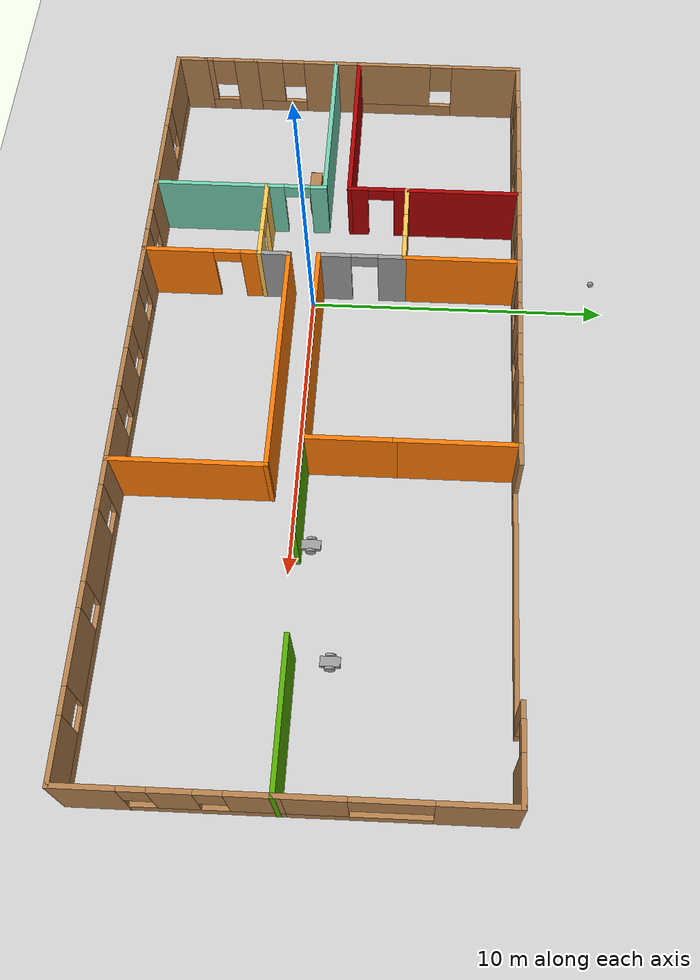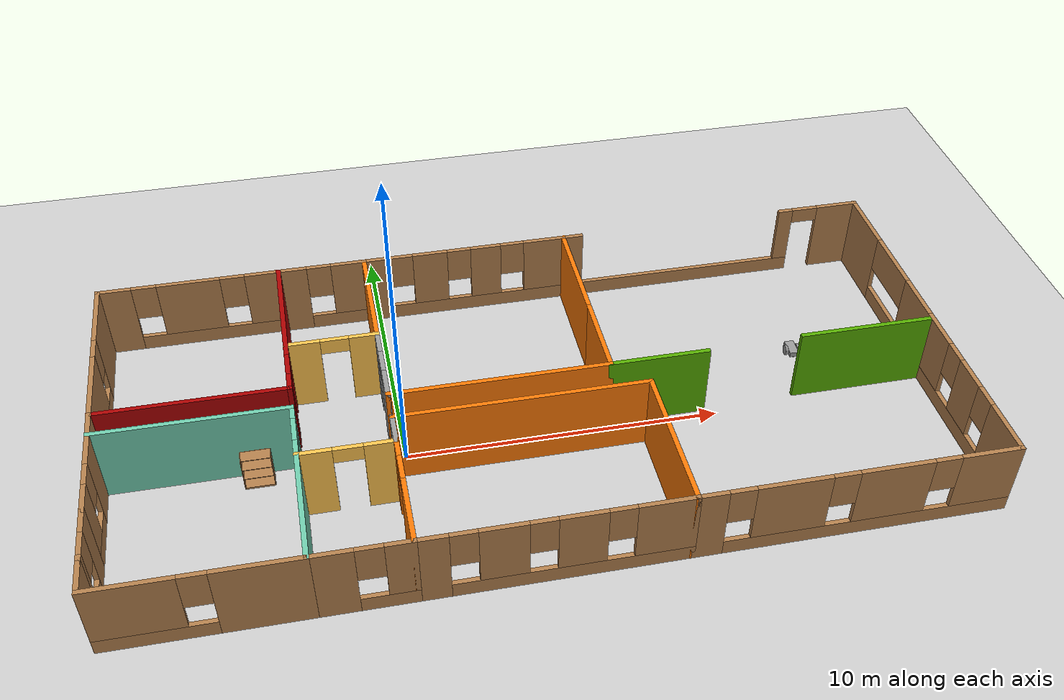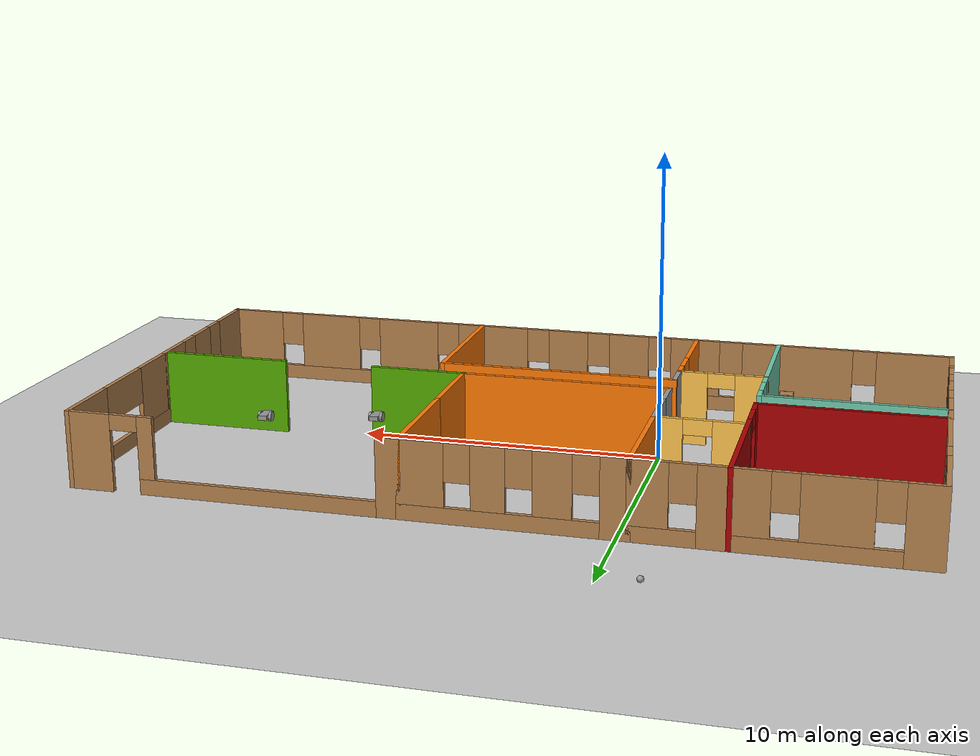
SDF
<sdf version="1.6">
 <world name="default">
  <plugin name="welcome" filename="libwelcome.so"/>
  <light name="sun" type="directional">
   <pose>0 0 10 0 -0 0</pose>
   <diffuse>0.8 0.8 0.8 1</diffuse>
   <specular>0.2 0.2 0.2 1</specular>
   <attenuation>
    <range>1000</range>
    <constant>0.9</constant>
    <linear>0.01</linear>
    <quadratic>0.001</quadratic>
   </attenuation>
   <direction>-0.5 0.1 -0.9</direction>
  </light>
  <model name="ground_plane">
   <static>1</static>
   <link name="link">
    <collision name="collision">
     <geometry><plane><normal>0 0 1</normal><size>100 100</size></plane></geometry>
     <surface>
      <contact><collide_bitmask>65535</collide_bitmask></contact>
      <friction><ode><mu>100</mu><mu2>50</mu2></ode></friction>
     </surface>
    </collision>
    <visual name="visual">
     <cast_shadows>0</cast_shadows>
     <geometry><plane><normal>0 0 1</normal><size>100 100</size></plane></geometry>
     <material>
      <script><uri>file://media/materials/scripts/gazebo.material</uri><name>Gazebo/Grey</name></script>
     </material>
    </visual>
   </link>
  </model>
  <gravity>0 0 -9.8</gravity>
  <magnetic_field>6e-06 2.3e-05 -4.2e-05</magnetic_field>
  <atmosphere type="adiabatic"/>
  <physics name="default_physics" default="0" type="ode">
   <max_step_size>0.001</max_step_size>
   <real_time_factor>1</real_time_factor>
   <real_time_update_rate>1000</real_time_update_rate>
  </physics>
  <scene><ambient>0.4 0.4 0.4 1</ambient><background>0.7 0.7 0.7 1</background><shadows>1</shadows></scene>
  <spherical_coordinates>
   <surface_model>EARTH_WGS84</surface_model>
   <latitude_deg>0</latitude_deg>
   <longitude_deg>0</longitude_deg>
   <elevation>0</elevation>
   <heading_deg>0</heading_deg>
  </spherical_coordinates>
  <model name="home">
   <pose>4.0109 0.7129 0 0 -0 0</pose>
   <link name="Wall_24">
    <pose>-13.075 3.35 0 0 0 -1.5708</pose>
    <visual name="Wall_24_Visual_0">
     <pose>-1.74921 0 1.25 0 -0 0</pose>
     <geometry><box><size>2.50157 0.15 2.5</size></box></geometry>
     <material>
      <script><uri>file://media/materials/scripts/gazebo.material</uri><name>Gazebo/Wood</name></script>
      <ambient>1 1 1 1</ambient>
     </material>
     <meta><layer>0</layer></meta>
    </visual>
    <collision name="Wall_24_Collision_0">
     <geometry><box><size>2.50157 0.15 2.5</size></box></geometry>
     <pose>-1.74921 0 1.25 0 -0 0</pose>
    </collision>
    <visual name="Wall_24_Visual_1">
     <pose>1.25079 0 0.25 0 -0 0</pose>
     <geometry><box><size>3.49843 0.15 0.5</size></box></geometry>
     <material>
      <script><uri>file://media/materials/scripts/gazebo.material</uri><name>Gazebo/Wood</name></script>
      <ambient>1 1 1 1</ambient>
     </material>
     <meta><layer>0</layer></meta>
    </visual>
    <collision name="Wall_24_Collision_1">
     <geometry><box><size>3.49843 0.15 0.5</size></box></geometry>
     <pose>1.25079 0 0.25 0 -0 0</pose>
    </collision>
    <visual name="Wall_24_Visual_2">
     <pose>1.65078 0 1.5 0 -0 0</pose>
     <geometry><box><size>2.69843 0.15 2</size></box></geometry>
     <material>
      <script><uri>file://media/materials/scripts/gazebo.material</uri><name>Gazebo/Wood</name></script>
      <ambient>1 1 1 1</ambient>
     </material>
     <meta><layer>0</layer></meta>
    </visual>
    <collision name="Wall_24_Collision_2">
     <geometry><box><size>2.69843 0.15 2</size></box></geometry>
     <pose>1.65078 0 1.5 0 -0 0</pose>
    </collision>
    <visual name="Wall_24_Visual_3">
     <pose>-0.098431 0 1.9 0 -0 0</pose>
     <geometry><box><size>0.8 0.15 1.2</size></box></geometry>
     <material>
      <script><uri>file://media/materials/scripts/gazebo.material</uri><name>Gazebo/Wood</name></script>
      <ambient>1 1 1 1</ambient>
     </material>
     <meta><layer>0</layer></meta>
    </visual>
    <collision name="Wall_24_Collision_3">
     <geometry><box><size>0.8 0.15 1.2</size></box></geometry>
     <pose>-0.098431 0 1.9 0 -0 0</pose>
    </collision>
   </link>
   <link name="Wall_25">
    <collision name="Wall_25_Collision">
     <geometry><box><size>6 0.15 2.5</size></box></geometry>
     <pose>0 0 1.25 0 -0 0</pose>
    </collision>
    <visual name="Wall_25_Visual">
     <pose>0 0 1.25 0 -0 0</pose>
     <geometry><box><size>6 0.15 2.5</size></box></geometry>
     <material>
      <script><uri>file://media/materials/scripts/gazebo.material</uri><name>Gazebo/Grey</name></script>
      <ambient>0.666667 0 0 1</ambient>
     </material>
     <meta><layer>0</layer></meta>
    </visual>
    <pose>-10.15 0.425 0 0 -0 0</pose>
   </link>
   <link name="Wall_27">
    <pose>-10.15 6.275 0 0 -0 0</pose>
    <visual name="Wall_27_Visual_0">
     <pose>-2.4286 0 1.25 0 -0 0</pose>
     <geometry><box><size>1.1428 0.15 2.5</size></box></geometry>
     <material>
      <script><uri>file://media/materials/scripts/gazebo.material</uri><name>Gazebo/Wood</name></script>
      <ambient>1 1 1 1</ambient>
     </material>
     <meta><layer>0</layer></meta>
    </visual>
    <collision name="Wall_27_Collision_0">
     <geometry><box><size>1.1428 0.15 2.5</size></box></geometry>
     <pose>-2.4286 0 1.25 0 -0 0</pose>
    </collision>
    <visual name="Wall_27_Visual_1">
     <pose>0.571398 0 0.25 0 -0 0</pose>
     <geometry><box><size>4.8572 0.15 0.5</size></box></geometry>
     <material>
      <script><uri>file://media/materials/scripts/gazebo.material</uri><name>Gazebo/Wood</name></script>
      <ambient>1 1 1 1</ambient>
     </material>
     <meta><layer>0</layer></meta>
    </visual>
    <collision name="Wall_27_Collision_1">
     <geometry><box><size>4.8572 0.15 0.5</size></box></geometry>
     <pose>0.571398 0 0.25 0 -0 0</pose>
    </collision>
    <visual name="Wall_27_Visual_2">
     <pose>-0.031204 0 1.5 0 -0 0</pose>
     <geometry><box><size>2.052 0.15 2</size></box></geometry>
     <material>
      <script><uri>file://media/materials/scripts/gazebo.material</uri><name>Gazebo/Wood</name></script>
      <ambient>1 1 1 1</ambient>
     </material>
     <meta><layer>0</layer></meta>
    </visual>
    <collision name="Wall_27_Collision_2">
     <geometry><box><size>2.052 0.15 2</size></box></geometry>
     <pose>-0.031204 0 1.5 0 -0 0</pose>
    </collision>
    <visual name="Wall_27_Visual_3">
     <pose>2.3974 0 1.5 0 -0 0</pose>
     <geometry><box><size>1.2052 0.15 2</size></box></geometry>
     <material>
      <script><uri>file://media/materials/scripts/gazebo.material</uri><name>Gazebo/Wood</name></script>
      <ambient>1 1 1 1</ambient>
     </material>
     <meta><layer>0</layer></meta>
    </visual>
    <collision name="Wall_27_Collision_3">
     <geometry><box><size>1.2052 0.15 2</size></box></geometry>
     <pose>2.3974 0 1.5 0 -0 0</pose>
    </collision>
    <visual name="Wall_27_Visual_4">
     <pose>-1.4572 0 1.9 0 -0 0</pose>
     <geometry><box><size>0.8 0.15 1.2</size></box></geometry>
     <material>
      <script><uri>file://media/materials/scripts/gazebo.material</uri><name>Gazebo/Wood</name></script>
      <ambient>1 1 1 1</ambient>
     </material>
     <meta><layer>0</layer></meta>
    </visual>
    <collision name="Wall_27_Collision_4">
     <geometry><box><size>0.8 0.15 1.2</size></box></geometry>
     <pose>-1.4572 0 1.9 0 -0 0</pose>
    </collision>
    <visual name="Wall_27_Visual_5">
     <pose>1.3948 0 1.9 0 -0 0</pose>
     <geometry><box><size>0.8 0.15 1.2</size></box></geometry>
     <material>
      <script><uri>file://media/materials/scripts/gazebo.material</uri><name>Gazebo/Wood</name></script>
      <ambient>1 1 1 1</ambient>
     </material>
     <meta><layer>0</layer></meta>
    </visual>
    <collision name="Wall_27_Collision_5">
     <geometry><box><size>0.8 0.15 1.2</size></box></geometry>
     <pose>1.3948 0 1.9 0 -0 0</pose>
    </collision>
   </link>
   <link name="Wall_28">
    <pose>-7.225 3.35 0 0 0 -1.5708</pose>
    <visual name="Wall_28_Visual_0">
     <pose>-0.808215 0 1.25 0 -0 0</pose>
     <geometry><box><size>4.38357 0.15 2.5</size></box></geometry>
     <material>
      <script><uri>file://media/materials/scripts/gazebo.material</uri><name>Gazebo/Grey</name></script>
      <ambient>0.666667 0 0 1</ambient>
     </material>
     <meta><layer>0</layer></meta>
    </visual>
    <collision name="Wall_28_Collision_0">
     <geometry><box><size>4.38357 0.15 2.5</size></box></geometry>
     <pose>-0.808215 0 1.25 0 -0 0</pose>
    </collision>
    <visual name="Wall_28_Visual_1">
     <pose>2.64179 0 1.25 0 -0 0</pose>
     <geometry><box><size>0.716431 0.15 2.5</size></box></geometry>
     <material>
      <script><uri>file://media/materials/scripts/gazebo.material</uri><name>Gazebo/Grey</name></script>
      <ambient>0.666667 0 0 1</ambient>
     </material>
     <meta><layer>0</layer></meta>
    </visual>
    <collision name="Wall_28_Collision_1">
     <geometry><box><size>0.716431 0.15 2.5</size></box></geometry>
     <pose>2.64179 0 1.25 0 -0 0</pose>
    </collision>
    <visual name="Wall_28_Visual_2">
     <pose>1.83357 0 2.25 0 -0 0</pose>
     <geometry><box><size>0.9 0.15 0.5</size></box></geometry>
     <material>
      <script><uri>file://media/materials/scripts/gazebo.material</uri><name>Gazebo/Grey</name></script>
      <ambient>0.666667 0 0 1</ambient>
     </material>
     <meta><layer>0</layer></meta>
    </visual>
    <collision name="Wall_28_Collision_2">
     <geometry><box><size>0.9 0.15 0.5</size></box></geometry>
     <pose>1.83357 0 2.25 0 -0 0</pose>
    </collision>
   </link>
   <link name="Wall_32">
    <pose>-13.075 -1.5 0 0 0 -1.5708</pose>
    <visual name="Wall_32_Visual_0">
     <pose>-0.937215 0 1.25 0 -0 0</pose>
     <geometry><box><size>2.12557 0.15 2.5</size></box></geometry>
     <material>
      <script><uri>file://media/materials/scripts/gazebo.material</uri><name>Gazebo/Wood</name></script>
      <ambient>1 1 1 1</ambient>
     </material>
     <meta><layer>0</layer></meta>
    </visual>
    <collision name="Wall_32_Collision_0">
     <geometry><box><size>2.12557 0.15 2.5</size></box></geometry>
     <pose>-0.937215 0 1.25 0 -0 0</pose>
    </collision>
    <visual name="Wall_32_Visual_1">
     <pose>1.06279 0 0.25 0 -0 0</pose>
     <geometry><box><size>1.87443 0.15 0.5</size></box></geometry>
     <material>
      <script><uri>file://media/materials/scripts/gazebo.material</uri><name>Gazebo/Wood</name></script>
      <ambient>1 1 1 1</ambient>
     </material>
     <meta><layer>0</layer></meta>
    </visual>
    <collision name="Wall_32_Collision_1">
     <geometry><box><size>1.87443 0.15 0.5</size></box></geometry>
     <pose>1.06279 0 0.25 0 -0 0</pose>
    </collision>
    <visual name="Wall_32_Visual_2">
     <pose>1.46279 0 1.5 0 -0 0</pose>
     <geometry><box><size>1.07443 0.15 2</size></box></geometry>
     <material>
      <script><uri>file://media/materials/scripts/gazebo.material</uri><name>Gazebo/Wood</name></script>
      <ambient>1 1 1 1</ambient>
     </material>
     <meta><layer>0</layer></meta>
    </visual>
    <collision name="Wall_32_Collision_2">
     <geometry><box><size>1.07443 0.15 2</size></box></geometry>
     <pose>1.46279 0 1.5 0 -0 0</pose>
    </collision>
    <visual name="Wall_32_Visual_3">
     <pose>0.525569 0 1.9 0 -0 0</pose>
     <geometry><box><size>0.8 0.15 1.2</size></box></geometry>
     <material>
      <script><uri>file://media/materials/scripts/gazebo.material</uri><name>Gazebo/Wood</name></script>
      <ambient>1 1 1 1</ambient>
     </material>
     <meta><layer>0</layer></meta>
    </visual>
    <collision name="Wall_32_Collision_3">
     <geometry><box><size>0.8 0.15 1.2</size></box></geometry>
     <pose>0.525569 0 1.9 0 -0 0</pose>
    </collision>
   </link>
   <link name="Wall_34">
    <pose>-13.075 -4.35 0 0 0 -1.5708</pose>
    <visual name="Wall_34_Visual_0">
     <pose>-0.574215 0 1.25 0 -0 0</pose>
     <geometry><box><size>0.85157 0.15 2.5</size></box></geometry>
     <material>
      <script><uri>file://media/materials/scripts/gazebo.material</uri><name>Gazebo/Wood</name></script>
      <ambient>1 1 1 1</ambient>
     </material>
     <meta><layer>0</layer></meta>
    </visual>
    <collision name="Wall_34_Collision_0">
     <geometry><box><size>0.85157 0.15 2.5</size></box></geometry>
     <pose>-0.574215 0 1.25 0 -0 0</pose>
    </collision>
    <visual name="Wall_34_Visual_1">
     <pose>0.425785 0 0.25 0 -0 0</pose>
     <geometry><box><size>1.14843 0.15 0.5</size></box></geometry>
     <material>
      <script><uri>file://media/materials/scripts/gazebo.material</uri><name>Gazebo/Wood</name></script>
      <ambient>1 1 1 1</ambient>
     </material>
     <meta><layer>0</layer></meta>
    </visual>
    <collision name="Wall_34_Collision_1">
     <geometry><box><size>1.14843 0.15 0.5</size></box></geometry>
     <pose>0.425785 0 0.25 0 -0 0</pose>
    </collision>
    <visual name="Wall_34_Visual_2">
     <pose>0.825785 0 1.5 0 -0 0</pose>
     <geometry><box><size>0.34843 0.15 2</size></box></geometry>
     <material>
      <script><uri>file://media/materials/scripts/gazebo.material</uri><name>Gazebo/Wood</name></script>
      <ambient>1 1 1 1</ambient>
     </material>
     <meta><layer>0</layer></meta>
    </visual>
    <collision name="Wall_34_Collision_2">
     <geometry><box><size>0.34843 0.15 2</size></box></geometry>
     <pose>0.825785 0 1.5 0 -0 0</pose>
    </collision>
    <visual name="Wall_34_Visual_3">
     <pose>0.25157 0 1.9 0 -0 0</pose>
     <geometry><box><size>0.8 0.15 1.2</size></box></geometry>
     <material>
      <script><uri>file://media/materials/scripts/gazebo.material</uri><name>Gazebo/Wood</name></script>
      <ambient>1 1 1 1</ambient>
     </material>
     <meta><layer>0</layer></meta>
    </visual>
    <collision name="Wall_34_Collision_3">
     <geometry><box><size>0.8 0.15 1.2</size></box></geometry>
     <pose>0.25157 0 1.9 0 -0 0</pose>
    </collision>
   </link>
   <link name="Wall_36">
    <collision name="Wall_36_Collision">
     <geometry><box><size>1 0.15 2.5</size></box></geometry>
     <pose>0 0 1.25 0 -0 0</pose>
    </collision>
    <visual name="Wall_36_Visual">
     <pose>0 0 1.25 0 -0 0</pose>
     <geometry><box><size>1 0.15 2.5</size></box></geometry>
     <material>
      <script><uri>file://media/materials/scripts/gazebo.material</uri><name>Gazebo/Wood</name></script>
      <ambient>1 1 1 1</ambient>
     </material>
     <meta><layer>0</layer></meta>
    </visual>
    <pose>-13.075 -5.7 0 0 0 -1.5708</pose>
   </link>
   <link name="Wall_39">
    <collision name="Wall_39_Collision">
     <geometry><box><size>6 0.15 2.5</size></box></geometry>
     <pose>0 0 1.25 0 -0 0</pose>
    </collision>
    <visual name="Wall_39_Visual">
     <pose>0 0 1.25 0 -0 0</pose>
     <geometry><box><size>6 0.15 2.5</size></box></geometry>
     <material>
      <script><uri>file://media/materials/scripts/gazebo.material</uri><name>Gazebo/Grey</name></script>
      <ambient>0.435294 0.796078 0.67451 1</ambient>
     </material>
     <meta><layer>0</layer></meta>
    </visual>
    <pose>-10.15 -0.425 0 0 -0 3.14159</pose>
   </link>
   <link name="Wall_43">
    <pose>-7.225 -3.35 0 0 0 -1.5708</pose>
    <visual name="Wall_43_Visual_0">
     <pose>-2.70921 0 1.25 0 -0 0</pose>
     <geometry><box><size>0.581569 0.15 2.5</size></box></geometry>
     <material>
      <script><uri>file://media/materials/scripts/gazebo.material</uri><name>Gazebo/Grey</name></script>
      <ambient>0.435294 0.796078 0.67451 1</ambient>
     </material>
     <meta><layer>0</layer></meta>
    </visual>
    <collision name="Wall_43_Collision_0">
     <geometry><box><size>0.581569 0.15 2.5</size></box></geometry>
     <pose>-2.70921 0 1.25 0 -0 0</pose>
    </collision>
    <visual name="Wall_43_Visual_1">
     <pose>0.740785 0 1.25 0 -0 0</pose>
     <geometry><box><size>4.51843 0.15 2.5</size></box></geometry>
     <material>
      <script><uri>file://media/materials/scripts/gazebo.material</uri><name>Gazebo/Grey</name></script>
      <ambient>0.435294 0.796078 0.67451 1</ambient>
     </material>
     <meta><layer>0</layer></meta>
    </visual>
    <collision name="Wall_43_Collision_1">
     <geometry><box><size>4.51843 0.15 2.5</size></box></geometry>
     <pose>0.740785 0 1.25 0 -0 0</pose>
    </collision>
    <visual name="Wall_43_Visual_2">
     <pose>-1.96843 0 2.25 0 -0 0</pose>
     <geometry><box><size>0.9 0.15 0.5</size></box></geometry>
     <material>
      <script><uri>file://media/materials/scripts/gazebo.material</uri><name>Gazebo/Grey</name></script>
      <ambient>0.435294 0.796078 0.67451 1</ambient>
     </material>
     <meta><layer>0</layer></meta>
    </visual>
    <collision name="Wall_43_Collision_2">
     <geometry><box><size>0.9 0.15 0.5</size></box></geometry>
     <pose>-1.96843 0 2.25 0 -0 0</pose>
    </collision>
   </link>
   <link name="Wall_44">
    <pose>-10.15 -6.275 0 0 -0 3.14159</pose>
    <visual name="Wall_44_Visual_0">
     <pose>-1.6844 0 1.25 0 -0 0</pose>
     <geometry><box><size>2.6312 0.15 2.5</size></box></geometry>
     <material>
      <script><uri>file://media/materials/scripts/gazebo.material</uri><name>Gazebo/Wood</name></script>
      <ambient>1 1 1 1</ambient>
     </material>
     <meta><layer>0</layer></meta>
    </visual>
    <collision name="Wall_44_Collision_0">
     <geometry><box><size>2.6312 0.15 2.5</size></box></geometry>
     <pose>-1.6844 0 1.25 0 -0 0</pose>
    </collision>
    <visual name="Wall_44_Visual_1">
     <pose>1.3156 0 0.25 0 -0 0</pose>
     <geometry><box><size>3.3688 0.15 0.5</size></box></geometry>
     <material>
      <script><uri>file://media/materials/scripts/gazebo.material</uri><name>Gazebo/Wood</name></script>
      <ambient>1 1 1 1</ambient>
     </material>
     <meta><layer>0</layer></meta>
    </visual>
    <collision name="Wall_44_Collision_1">
     <geometry><box><size>3.3688 0.15 0.5</size></box></geometry>
     <pose>1.3156 0 0.25 0 -0 0</pose>
    </collision>
    <visual name="Wall_44_Visual_2">
     <pose>1.7156 0 1.5 0 -0 0</pose>
     <geometry><box><size>2.5688 0.15 2</size></box></geometry>
     <material>
      <script><uri>file://media/materials/scripts/gazebo.material</uri><name>Gazebo/Wood</name></script>
      <ambient>1 1 1 1</ambient>
     </material>
     <meta><layer>0</layer></meta>
    </visual>
    <collision name="Wall_44_Collision_2">
     <geometry><box><size>2.5688 0.15 2</size></box></geometry>
     <pose>1.7156 0 1.5 0 -0 0</pose>
    </collision>
    <visual name="Wall_44_Visual_3">
     <pose>0.031204 0 1.9 0 -0 0</pose>
     <geometry><box><size>0.8 0.15 1.2</size></box></geometry>
     <material>
      <script><uri>file://media/materials/scripts/gazebo.material</uri><name>Gazebo/Wood</name></script>
      <ambient>1 1 1 1</ambient>
     </material>
     <meta><layer>0</layer></meta>
    </visual>
    <collision name="Wall_44_Collision_3">
     <geometry><box><size>0.8 0.15 1.2</size></box></geometry>
     <pose>0.031204 0 1.9 0 -0 0</pose>
    </collision>
   </link>
   <link name="Wall_48">
    <pose>-5.8 6.275 0 0 -0 0</pose>
    <visual name="Wall_48_Visual_0">
     <pose>-1.0016 0 1.25 0 -0 0</pose>
     <geometry><box><size>0.996796 0.15 2.5</size></box></geometry>
     <material>
      <script><uri>file://media/materials/scripts/gazebo.material</uri><name>Gazebo/Wood</name></script>
      <ambient>1 1 1 1</ambient>
     </material>
     <meta><layer>0</layer></meta>
    </visual>
    <collision name="Wall_48_Collision_0">
     <geometry><box><size>0.996796 0.15 2.5</size></box></geometry>
     <pose>-1.0016 0 1.25 0 -0 0</pose>
    </collision>
    <visual name="Wall_48_Visual_1">
     <pose>0.498398 0 0.25 0 -0 0</pose>
     <geometry><box><size>2.0032 0.15 0.5</size></box></geometry>
     <material>
      <script><uri>file://media/materials/scripts/gazebo.material</uri><name>Gazebo/Wood</name></script>
      <ambient>1 1 1 1</ambient>
     </material>
     <meta><layer>0</layer></meta>
    </visual>
    <collision name="Wall_48_Collision_1">
     <geometry><box><size>2.0032 0.15 0.5</size></box></geometry>
     <pose>0.498398 0 0.25 0 -0 0</pose>
    </collision>
    <visual name="Wall_48_Visual_2">
     <pose>0.898398 0 1.5 0 -0 0</pose>
     <geometry><box><size>1.2032 0.15 2</size></box></geometry>
     <material>
      <script><uri>file://media/materials/scripts/gazebo.material</uri><name>Gazebo/Wood</name></script>
      <ambient>1 1 1 1</ambient>
     </material>
     <meta><layer>0</layer></meta>
    </visual>
    <collision name="Wall_48_Collision_2">
     <geometry><box><size>1.2032 0.15 2</size></box></geometry>
     <pose>0.898398 0 1.5 0 -0 0</pose>
    </collision>
    <visual name="Wall_48_Visual_3">
     <pose>-0.103204 0 1.9 0 -0 0</pose>
     <geometry><box><size>0.8 0.15 1.2</size></box></geometry>
     <material>
      <script><uri>file://media/materials/scripts/gazebo.material</uri><name>Gazebo/Wood</name></script>
      <ambient>1 1 1 1</ambient>
     </material>
     <meta><layer>0</layer></meta>
    </visual>
    <collision name="Wall_48_Collision_3">
     <geometry><box><size>0.8 0.15 1.2</size></box></geometry>
     <pose>-0.103204 0 1.9 0 -0 0</pose>
    </collision>
   </link>
   <link name="Wall_49">
    <collision name="Wall_49_Collision">
     <geometry><box><size>4 0.15 2.5</size></box></geometry>
     <pose>0 0 1.25 0 -0 0</pose>
    </collision>
    <visual name="Wall_49_Visual">
     <pose>0 0 1.25 0 -0 0</pose>
     <geometry><box><size>4 0.15 2.5</size></box></geometry>
     <material>
      <script><uri>file://media/materials/scripts/gazebo.material</uri><name>Gazebo/Grey</name></script>
      <ambient>0.996078 0.47451 0.0196078 1</ambient>
     </material>
     <meta><layer>0</layer></meta>
    </visual>
    <pose>-4.375 4.35 0 0 0 -1.5708</pose>
   </link>
   <link name="Wall_50">
    <pose>-5.8 2.425 0 0 -0 3.14159</pose>
    <visual name="Wall_50_Visual_0">
     <pose>-1.0154 0 1.25 0 -0 0</pose>
     <geometry><box><size>0.969204 0.15 2.5</size></box></geometry>
     <material>
      <script><uri>file://media/materials/scripts/gazebo.material</uri><name>Gazebo/Grey</name></script>
      <ambient>1 0.764706 0.305882 1</ambient>
     </material>
     <meta><layer>0</layer></meta>
    </visual>
    <collision name="Wall_50_Collision_0">
     <geometry><box><size>0.969204 0.15 2.5</size></box></geometry>
     <pose>-1.0154 0 1.25 0 -0 0</pose>
    </collision>
    <visual name="Wall_50_Visual_1">
     <pose>0.934602 0 1.25 0 -0 0</pose>
     <geometry><box><size>1.1308 0.15 2.5</size></box></geometry>
     <material>
      <script><uri>file://media/materials/scripts/gazebo.material</uri><name>Gazebo/Grey</name></script>
      <ambient>1 0.764706 0.305882 1</ambient>
     </material>
     <meta><layer>0</layer></meta>
    </visual>
    <collision name="Wall_50_Collision_1">
     <geometry><box><size>1.1308 0.15 2.5</size></box></geometry>
     <pose>0.934602 0 1.25 0 -0 0</pose>
    </collision>
    <visual name="Wall_50_Visual_2">
     <pose>-0.080796 0 2.25 0 -0 0</pose>
     <geometry><box><size>0.9 0.15 0.5</size></box></geometry>
     <material>
      <script><uri>file://media/materials/scripts/gazebo.material</uri><name>Gazebo/Grey</name></script>
      <ambient>1 0.764706 0.305882 1</ambient>
     </material>
     <meta><layer>0</layer></meta>
    </visual>
    <collision name="Wall_50_Collision_2">
     <geometry><box><size>0.9 0.15 0.5</size></box></geometry>
     <pose>-0.080796 0 2.25 0 -0 0</pose>
    </collision>
   </link>
   <link name="Wall_53">
    <pose>-0.95 6.275 0 0 -0 0</pose>
    <visual name="Wall_53_Visual_0">
     <pose>-3.0466 0 1.25 0 -0 0</pose>
     <geometry><box><size>0.906796 0.15 2.5</size></box></geometry>
     <material>
      <script><uri>file://media/materials/scripts/gazebo.material</uri><name>Gazebo/Wood</name></script>
      <ambient>1 1 1 1</ambient>
     </material>
     <meta><layer>0</layer></meta>
    </visual>
    <collision name="Wall_53_Collision_0">
     <geometry><box><size>0.906796 0.15 2.5</size></box></geometry>
     <pose>-3.0466 0 1.25 0 -0 0</pose>
    </collision>
    <visual name="Wall_53_Visual_1">
     <pose>0.453398 0 0.25 0 -0 0</pose>
     <geometry><box><size>6.0932 0.15 0.5</size></box></geometry>
     <material>
      <script><uri>file://media/materials/scripts/gazebo.material</uri><name>Gazebo/Wood</name></script>
      <ambient>1 1 1 1</ambient>
     </material>
     <meta><layer>0</layer></meta>
    </visual>
    <collision name="Wall_53_Collision_1">
     <geometry><box><size>6.0932 0.15 0.5</size></box></geometry>
     <pose>0.453398 0 0.25 0 -0 0</pose>
    </collision>
    <visual name="Wall_53_Visual_2">
     <pose>-1.2042 0 1.5 0 -0 0</pose>
     <geometry><box><size>1.178 0.15 2</size></box></geometry>
     <material>
      <script><uri>file://media/materials/scripts/gazebo.material</uri><name>Gazebo/Wood</name></script>
      <ambient>1 1 1 1</ambient>
     </material>
     <meta><layer>0</layer></meta>
    </visual>
    <collision name="Wall_53_Collision_2">
     <geometry><box><size>1.178 0.15 2</size></box></geometry>
     <pose>-1.2042 0 1.5 0 -0 0</pose>
    </collision>
    <visual name="Wall_53_Visual_3">
     <pose>0.704796 0 1.5 0 -0 0</pose>
     <geometry><box><size>1.04 0.15 2</size></box></geometry>
     <material>
      <script><uri>file://media/materials/scripts/gazebo.material</uri><name>Gazebo/Wood</name></script>
      <ambient>1 1 1 1</ambient>
     </material>
     <meta><layer>0</layer></meta>
    </visual>
    <collision name="Wall_53_Collision_3">
     <geometry><box><size>1.04 0.15 2</size></box></geometry>
     <pose>0.704796 0 1.5 0 -0 0</pose>
    </collision>
    <visual name="Wall_53_Visual_4">
     <pose>2.7624 0 1.5 0 -0 0</pose>
     <geometry><box><size>1.4752 0.15 2</size></box></geometry>
     <material>
      <script><uri>file://media/materials/scripts/gazebo.material</uri><name>Gazebo/Wood</name></script>
      <ambient>1 1 1 1</ambient>
     </material>
     <meta><layer>0</layer></meta>
    </visual>
    <collision name="Wall_53_Collision_4">
     <geometry><box><size>1.4752 0.15 2</size></box></geometry>
     <pose>2.7624 0 1.5 0 -0 0</pose>
    </collision>
    <visual name="Wall_53_Visual_5">
     <pose>-2.1932 0 1.9 0 -0 0</pose>
     <geometry><box><size>0.8 0.15 1.2</size></box></geometry>
     <material>
      <script><uri>file://media/materials/scripts/gazebo.material</uri><name>Gazebo/Wood</name></script>
      <ambient>1 1 1 1</ambient>
     </material>
     <meta><layer>0</layer></meta>
    </visual>
    <collision name="Wall_53_Collision_5">
     <geometry><box><size>0.8 0.15 1.2</size></box></geometry>
     <pose>-2.1932 0 1.9 0 -0 0</pose>
    </collision>
    <visual name="Wall_53_Visual_6">
     <pose>-0.215204 0 1.9 0 -0 0</pose>
     <geometry><box><size>0.8 0.15 1.2</size></box></geometry>
     <material>
      <script><uri>file://media/materials/scripts/gazebo.material</uri><name>Gazebo/Wood</name></script>
      <ambient>1 1 1 1</ambient>
     </material>
     <meta><layer>0</layer></meta>
    </visual>
    <collision name="Wall_53_Collision_6">
     <geometry><box><size>0.8 0.15 1.2</size></box></geometry>
     <pose>-0.215204 0 1.9 0 -0 0</pose>
    </collision>
    <visual name="Wall_53_Visual_7">
     <pose>1.6248 0 1.9 0 -0 0</pose>
     <geometry><box><size>0.8 0.15 1.2</size></box></geometry>
     <material>
      <script><uri>file://media/materials/scripts/gazebo.material</uri><name>Gazebo/Wood</name></script>
      <ambient>1 1 1 1</ambient>
     </material>
     <meta><layer>0</layer></meta>
    </visual>
    <collision name="Wall_53_Collision_7">
     <geometry><box><size>0.8 0.15 1.2</size></box></geometry>
     <pose>1.6248 0 1.9 0 -0 0</pose>
    </collision>
   </link>
   <link name="Wall_54">
    <collision name="Wall_54_Collision">
     <geometry><box><size>4 0.15 2.5</size></box></geometry>
     <pose>0 0 1.25 0 -0 0</pose>
    </collision>
    <visual name="Wall_54_Visual">
     <pose>0 0 1.25 0 -0 0</pose>
     <geometry><box><size>4 0.15 2.5</size></box></geometry>
     <material>
      <script><uri>file://media/materials/scripts/gazebo.material</uri><name>Gazebo/Grey</name></script>
      <ambient>0.996078 0.47451 0.0196078 1</ambient>
     </material>
     <meta><layer>0</layer></meta>
    </visual>
    <pose>2.475 4.35 0 0 0 -1.5708</pose>
   </link>
   <link name="Wall_56">
    <collision name="Wall_56_Collision">
     <geometry><box><size>3 0.15 2.5</size></box></geometry>
     <pose>0 0 1.25 0 -0 0</pose>
    </collision>
    <visual name="Wall_56_Visual">
     <pose>0 0 1.25 0 -0 0</pose>
     <geometry><box><size>3 0.15 2.5</size></box></geometry>
     <material>
      <script><uri>file://media/materials/scripts/gazebo.material</uri><name>Gazebo/Grey</name></script>
      <ambient>0.996078 0.47451 0.0196078 1</ambient>
     </material>
     <meta><layer>0</layer></meta>
    </visual>
    <pose>2.475 1 0 0 0 -1.5708</pose>
   </link>
   <link name="Wall_58">
    <pose>-4.375 1 0 0 0 -1.5708</pose>
    <visual name="Wall_58_Visual_0">
     <pose>-1.02622 0 1.25 0 -0 0</pose>
     <geometry><box><size>0.947569 0.15 2.5</size></box></geometry>
     <material>
      <script><uri>file://media/materials/scripts/gazebo.material</uri><name>Gazebo/Grey</name></script>
      <ambient>1 1 1 1</ambient>
     </material>
     <meta><layer>0</layer></meta>
    </visual>
    <collision name="Wall_58_Collision_0">
     <geometry><box><size>0.947569 0.15 2.5</size></box></geometry>
     <pose>-1.02622 0 1.25 0 -0 0</pose>
    </collision>
    <visual name="Wall_58_Visual_1">
     <pose>0.923785 0 1.25 0 -0 0</pose>
     <geometry><box><size>1.15243 0.15 2.5</size></box></geometry>
     <material>
      <script><uri>file://media/materials/scripts/gazebo.material</uri><name>Gazebo/Grey</name></script>
      <ambient>1 1 1 1</ambient>
     </material>
     <meta><layer>0</layer></meta>
    </visual>
    <collision name="Wall_58_Collision_1">
     <geometry><box><size>1.15243 0.15 2.5</size></box></geometry>
     <pose>0.923785 0 1.25 0 -0 0</pose>
    </collision>
    <visual name="Wall_58_Visual_2">
     <pose>-0.102431 0 2.25 0 -0 0</pose>
     <geometry><box><size>0.9 0.15 0.5</size></box></geometry>
     <material>
      <script><uri>file://media/materials/scripts/gazebo.material</uri><name>Gazebo/Grey</name></script>
      <ambient>1 1 1 1</ambient>
     </material>
     <meta><layer>0</layer></meta>
    </visual>
    <collision name="Wall_58_Collision_2">
     <geometry><box><size>0.9 0.15 0.5</size></box></geometry>
     <pose>-0.102431 0 2.25 0 -0 0</pose>
    </collision>
   </link>
   <link name="Wall_59">
    <collision name="Wall_59_Collision">
     <geometry><box><size>7 0.15 2.5</size></box></geometry>
     <pose>0 0 1.25 0 -0 0</pose>
    </collision>
    <visual name="Wall_59_Visual">
     <pose>0 0 1.25 0 -0 0</pose>
     <geometry><box><size>7 0.15 2.5</size></box></geometry>
     <material>
      <script><uri>file://media/materials/scripts/gazebo.material</uri><name>Gazebo/Grey</name></script>
      <ambient>0.996078 0.47451 0.0196078 1</ambient>
     </material>
     <meta><layer>0</layer></meta>
    </visual>
    <pose>-0.95 -0.425 0 0 -0 0</pose>
   </link>
   <link name="Wall_62">
    <pose>-5.8 -6.275 0 0 -0 0</pose>
    <visual name="Wall_62_Visual_0">
     <pose>-0.840602 0 1.25 0 -0 0</pose>
     <geometry><box><size>1.3188 0.15 2.5</size></box></geometry>
     <material>
      <script><uri>file://media/materials/scripts/gazebo.material</uri><name>Gazebo/Wood</name></script>
      <ambient>1 1 1 1</ambient>
     </material>
     <meta><layer>0</layer></meta>
    </visual>
    <collision name="Wall_62_Collision_0">
     <geometry><box><size>1.3188 0.15 2.5</size></box></geometry>
     <pose>-0.840602 0 1.25 0 -0 0</pose>
    </collision>
    <visual name="Wall_62_Visual_1">
     <pose>0.659398 0 0.25 0 -0 0</pose>
     <geometry><box><size>1.6812 0.15 0.5</size></box></geometry>
     <material>
      <script><uri>file://media/materials/scripts/gazebo.material</uri><name>Gazebo/Wood</name></script>
      <ambient>1 1 1 1</ambient>
     </material>
     <meta><layer>0</layer></meta>
    </visual>
    <collision name="Wall_62_Collision_1">
     <geometry><box><size>1.6812 0.15 0.5</size></box></geometry>
     <pose>0.659398 0 0.25 0 -0 0</pose>
    </collision>
    <visual name="Wall_62_Visual_2">
     <pose>1.0594 0 1.5 0 -0 0</pose>
     <geometry><box><size>0.881204 0.15 2</size></box></geometry>
     <material>
      <script><uri>file://media/materials/scripts/gazebo.material</uri><name>Gazebo/Wood</name></script>
      <ambient>1 1 1 1</ambient>
     </material>
     <meta><layer>0</layer></meta>
    </visual>
    <collision name="Wall_62_Collision_2">
     <geometry><box><size>0.881204 0.15 2</size></box></geometry>
     <pose>1.0594 0 1.5 0 -0 0</pose>
    </collision>
    <visual name="Wall_62_Visual_3">
     <pose>0.218796 0 1.9 0 -0 0</pose>
     <geometry><box><size>0.8 0.15 1.2</size></box></geometry>
     <material>
      <script><uri>file://media/materials/scripts/gazebo.material</uri><name>Gazebo/Wood</name></script>
      <ambient>1 1 1 1</ambient>
     </material>
     <meta><layer>0</layer></meta>
    </visual>
    <collision name="Wall_62_Collision_3">
     <geometry><box><size>0.8 0.15 1.2</size></box></geometry>
     <pose>0.218796 0 1.9 0 -0 0</pose>
    </collision>
   </link>
   <link name="Wall_63">
    <pose>-4.375 -4.35 0 0 -0 1.5708</pose>
    <visual name="Wall_63_Visual_0">
     <pose>-0.798785 0 1.25 0 -0 0</pose>
     <geometry><box><size>2.40243 0.15 2.5</size></box></geometry>
     <material>
      <script><uri>file://media/materials/scripts/gazebo.material</uri><name>Gazebo/Grey</name></script>
      <ambient>0.996078 0.47451 0.0196078 1</ambient>
     </material>
     <meta><layer>0</layer></meta>
    </visual>
    <collision name="Wall_63_Collision_0">
     <geometry><box><size>2.40243 0.15 2.5</size></box></geometry>
     <pose>-0.798785 0 1.25 0 -0 0</pose>
    </collision>
    <visual name="Wall_63_Visual_1">
     <pose>1.65122 0 1.25 0 -0 0</pose>
     <geometry><box><size>0.697569 0.15 2.5</size></box></geometry>
     <material>
      <script><uri>file://media/materials/scripts/gazebo.material</uri><name>Gazebo/Grey</name></script>
      <ambient>0.996078 0.47451 0.0196078 1</ambient>
     </material>
     <meta><layer>0</layer></meta>
    </visual>
    <collision name="Wall_63_Collision_1">
     <geometry><box><size>0.697569 0.15 2.5</size></box></geometry>
     <pose>1.65122 0 1.25 0 -0 0</pose>
    </collision>
    <visual name="Wall_63_Visual_2">
     <pose>0.852431 0 2.25 0 -0 0</pose>
     <geometry><box><size>0.9 0.15 0.5</size></box></geometry>
     <material>
      <script><uri>file://media/materials/scripts/gazebo.material</uri><name>Gazebo/Grey</name></script>
      <ambient>0.996078 0.47451 0.0196078 1</ambient>
     </material>
     <meta><layer>0</layer></meta>
    </visual>
    <collision name="Wall_63_Collision_2">
     <geometry><box><size>0.9 0.15 0.5</size></box></geometry>
     <pose>0.852431 0 2.25 0 -0 0</pose>
    </collision>
   </link>
   <link name="Wall_64">
    <pose>-5.8 -2.425 0 0 -0 3.14159</pose>
    <visual name="Wall_64_Visual_0">
     <pose>-0.992398 0 1.25 0 -0 0</pose>
     <geometry><box><size>1.0152 0.15 2.5</size></box></geometry>
     <material>
      <script><uri>file://media/materials/scripts/gazebo.material</uri><name>Gazebo/Grey</name></script>
      <ambient>1 0.764706 0.305882 1</ambient>
     </material>
     <meta><layer>0</layer></meta>
    </visual>
    <collision name="Wall_64_Collision_0">
     <geometry><box><size>1.0152 0.15 2.5</size></box></geometry>
     <pose>-0.992398 0 1.25 0 -0 0</pose>
    </collision>
    <visual name="Wall_64_Visual_1">
     <pose>0.957602 0 1.25 0 -0 0</pose>
     <geometry><box><size>1.0848 0.15 2.5</size></box></geometry>
     <material>
      <script><uri>file://media/materials/scripts/gazebo.material</uri><name>Gazebo/Grey</name></script>
      <ambient>1 0.764706 0.305882 1</ambient>
     </material>
     <meta><layer>0</layer></meta>
    </visual>
    <collision name="Wall_64_Collision_1">
     <geometry><box><size>1.0848 0.15 2.5</size></box></geometry>
     <pose>0.957602 0 1.25 0 -0 0</pose>
    </collision>
    <visual name="Wall_64_Visual_2">
     <pose>-0.034796 0 2.25 0 -0 0</pose>
     <geometry><box><size>0.9 0.15 0.5</size></box></geometry>
     <material>
      <script><uri>file://media/materials/scripts/gazebo.material</uri><name>Gazebo/Grey</name></script>
      <ambient>1 0.764706 0.305882 1</ambient>
     </material>
     <meta><layer>0</layer></meta>
    </visual>
    <collision name="Wall_64_Collision_2">
     <geometry><box><size>0.9 0.15 0.5</size></box></geometry>
     <pose>-0.034796 0 2.25 0 -0 0</pose>
    </collision>
   </link>
   <link name="Wall_68">
    <pose>-0.45 -6.275 0 0 -0 0</pose>
    <visual name="Wall_68_Visual_0">
     <pose>-3.5006 0 1.25 0 -0 0</pose>
     <geometry><box><size>0.998796 0.15 2.5</size></box></geometry>
     <material>
      <script><uri>file://media/materials/scripts/gazebo.material</uri><name>Gazebo/Wood</name></script>
      <ambient>1 1 1 1</ambient>
     </material>
     <meta><layer>0</layer></meta>
    </visual>
    <collision name="Wall_68_Collision_0">
     <geometry><box><size>0.998796 0.15 2.5</size></box></geometry>
     <pose>-3.5006 0 1.25 0 -0 0</pose>
    </collision>
    <visual name="Wall_68_Visual_1">
     <pose>0.499398 0 0.25 0 -0 0</pose>
     <geometry><box><size>7.0012 0.15 0.5</size></box></geometry>
     <material>
      <script><uri>file://media/materials/scripts/gazebo.material</uri><name>Gazebo/Wood</name></script>
      <ambient>1 1 1 1</ambient>
     </material>
     <meta><layer>0</layer></meta>
    </visual>
    <collision name="Wall_68_Collision_1">
     <geometry><box><size>7.0012 0.15 0.5</size></box></geometry>
     <pose>0.499398 0 0.25 0 -0 0</pose>
    </collision>
    <visual name="Wall_68_Visual_2">
     <pose>-1.4972 0 1.5 0 -0 0</pose>
     <geometry><box><size>1.408 0.15 2</size></box></geometry>
     <material>
      <script><uri>file://media/materials/scripts/gazebo.material</uri><name>Gazebo/Wood</name></script>
      <ambient>1 1 1 1</ambient>
     </material>
     <meta><layer>0</layer></meta>
    </visual>
    <collision name="Wall_68_Collision_2">
     <geometry><box><size>1.408 0.15 2</size></box></geometry>
     <pose>-1.4972 0 1.5 0 -0 0</pose>
    </collision>
    <visual name="Wall_68_Visual_3">
     <pose>0.710796 0 1.5 0 -0 0</pose>
     <geometry><box><size>1.408 0.15 2</size></box></geometry>
     <material>
      <script><uri>file://media/materials/scripts/gazebo.material</uri><name>Gazebo/Wood</name></script>
      <ambient>1 1 1 1</ambient>
     </material>
     <meta><layer>0</layer></meta>
    </visual>
    <collision name="Wall_68_Collision_3">
     <geometry><box><size>1.408 0.15 2</size></box></geometry>
     <pose>0.710796 0 1.5 0 -0 0</pose>
    </collision>
    <visual name="Wall_68_Visual_4">
     <pose>3.1074 0 1.5 0 -0 0</pose>
     <geometry><box><size>1.7852 0.15 2</size></box></geometry>
     <material>
      <script><uri>file://media/materials/scripts/gazebo.material</uri><name>Gazebo/Wood</name></script>
      <ambient>1 1 1 1</ambient>
     </material>
     <meta><layer>0</layer></meta>
    </visual>
    <collision name="Wall_68_Collision_4">
     <geometry><box><size>1.7852 0.15 2</size></box></geometry>
     <pose>3.1074 0 1.5 0 -0 0</pose>
    </collision>
    <visual name="Wall_68_Visual_5">
     <pose>-2.6012 0 1.9 0 -0 0</pose>
     <geometry><box><size>0.8 0.15 1.2</size></box></geometry>
     <material>
      <script><uri>file://media/materials/scripts/gazebo.material</uri><name>Gazebo/Wood</name></script>
      <ambient>1 1 1 1</ambient>
     </material>
     <meta><layer>0</layer></meta>
    </visual>
    <collision name="Wall_68_Collision_5">
     <geometry><box><size>0.8 0.15 1.2</size></box></geometry>
     <pose>-2.6012 0 1.9 0 -0 0</pose>
    </collision>
    <visual name="Wall_68_Visual_6">
     <pose>-0.393204 0 1.9 0 -0 0</pose>
     <geometry><box><size>0.8 0.15 1.2</size></box></geometry>
     <material>
      <script><uri>file://media/materials/scripts/gazebo.material</uri><name>Gazebo/Wood</name></script>
      <ambient>1 1 1 1</ambient>
     </material>
     <meta><layer>0</layer></meta>
    </visual>
    <collision name="Wall_68_Collision_6">
     <geometry><box><size>0.8 0.15 1.2</size></box></geometry>
     <pose>-0.393204 0 1.9 0 -0 0</pose>
    </collision>
    <visual name="Wall_68_Visual_7">
     <pose>1.8148 0 1.9 0 -0 0</pose>
     <geometry><box><size>0.8 0.15 1.2</size></box></geometry>
     <material>
      <script><uri>file://media/materials/scripts/gazebo.material</uri><name>Gazebo/Wood</name></script>
      <ambient>1 1 1 1</ambient>
     </material>
     <meta><layer>0</layer></meta>
    </visual>
    <collision name="Wall_68_Collision_7">
     <geometry><box><size>0.8 0.15 1.2</size></box></geometry>
     <pose>1.8148 0 1.9 0 -0 0</pose>
    </collision>
   </link>
   <link name="Wall_69">
    <collision name="Wall_69_Collision">
     <geometry><box><size>5 0.15 2.5</size></box></geometry>
     <pose>0 0 1.25 0 -0 0</pose>
    </collision>
    <visual name="Wall_69_Visual">
     <pose>0 0 1.25 0 -0 0</pose>
     <geometry><box><size>5 0.15 2.5</size></box></geometry>
     <material>
      <script><uri>file://media/materials/scripts/gazebo.material</uri><name>Gazebo/Grey</name></script>
      <ambient>0.996078 0.47451 0.0196078 1</ambient>
     </material>
     <meta><layer>0</layer></meta>
    </visual>
    <pose>3.475 -3.85 0 0 -0 1.5708</pose>
   </link>
   <link name="Wall_70">
    <collision name="Wall_70_Collision">
     <geometry><box><size>8 0.15 2.5</size></box></geometry>
     <pose>0 0 1.25 0 -0 0</pose>
    </collision>
    <visual name="Wall_70_Visual">
     <pose>0 0 1.25 0 -0 0</pose>
     <geometry><box><size>8 0.15 2.5</size></box></geometry>
     <material>
      <script><uri>file://media/materials/scripts/gazebo.material</uri><name>Gazebo/Grey</name></script>
      <ambient>0.996078 0.47451 0.0196078 1</ambient>
     </material>
     <meta><layer>0</layer></meta>
    </visual>
    <pose>-0.45 -1.425 0 0 -0 3.14159</pose>
   </link>
   <link name="Wall_71">
    <collision name="Wall_71_Collision">
     <geometry><box><size>1.15 0.15 2.5</size></box></geometry>
     <pose>0 0 1.25 0 -0 0</pose>
    </collision>
    <visual name="Wall_71_Visual">
     <pose>0 0 1.25 0 -0 0</pose>
     <geometry><box><size>1.15 0.15 2.5</size></box></geometry>
     <material>
      <script><uri>file://media/materials/scripts/gazebo.material</uri><name>Gazebo/Grey</name></script>
      <ambient>1 1 1 1</ambient>
     </material>
     <meta><layer>0</layer></meta>
    </visual>
    <pose>-4.375 -1.925 0 0 0 -1.5708</pose>
   </link>
   <link name="Wall_74">
    <collision name="Wall_74_Collision">
     <geometry><box><size>3.25 0.15 2.5</size></box></geometry>
     <pose>0 0 1.25 0 -0 0</pose>
    </collision>
    <visual name="Wall_74_Visual">
     <pose>0 0 1.25 0 -0 0</pose>
     <geometry><box><size>3.25 0.15 2.5</size></box></geometry>
     <material>
      <script><uri>file://media/materials/scripts/gazebo.material</uri><name>Gazebo/Grey</name></script>
      <ambient>0.333333 0.666667 0 1</ambient>
     </material>
     <meta><layer>0</layer></meta>
    </visual>
    <pose>4.025 -0.425 0 0 -0 0</pose>
   </link>
   <link name="Wall_76">
    <pose>7.775 6.275 0 0 -0 0</pose>
    <visual name="Wall_76_Visual_0">
     <pose>-4.99493 0 1.25 0 -0 0</pose>
     <geometry><box><size>0.760131 0.15 2.5</size></box></geometry>
     <material>
      <script><uri>file://media/materials/scripts/gazebo.material</uri><name>Gazebo/Wood</name></script>
      <ambient>1 1 1 1</ambient>
     </material>
     <meta><layer>0</layer></meta>
    </visual>
    <collision name="Wall_76_Collision_0">
     <geometry><box><size>0.760131 0.15 2.5</size></box></geometry>
     <pose>-4.99493 0 1.25 0 -0 0</pose>
    </collision>
    <visual name="Wall_76_Visual_1">
     <pose>4.6294 0 1.25 0 -0 0</pose>
     <geometry><box><size>1.4912 0.15 2.5</size></box></geometry>
     <material>
      <script><uri>file://media/materials/scripts/gazebo.material</uri><name>Gazebo/Wood</name></script>
      <ambient>1 1 1 1</ambient>
     </material>
     <meta><layer>0</layer></meta>
    </visual>
    <collision name="Wall_76_Collision_1">
     <geometry><box><size>1.4912 0.15 2.5</size></box></geometry>
     <pose>4.6294 0 1.25 0 -0 0</pose>
    </collision>
    <visual name="Wall_76_Visual_2">
     <pose>-0.815537 0 0.25 0 -0 0</pose>
     <geometry><box><size>7.59866 0.15 0.5</size></box></geometry>
     <material>
      <script><uri>file://media/materials/scripts/gazebo.material</uri><name>Gazebo/Wood</name></script>
      <ambient>1 1 1 1</ambient>
     </material>
     <meta><layer>0</layer></meta>
    </visual>
    <collision name="Wall_76_Collision_2">
     <geometry><box><size>7.59866 0.15 0.5</size></box></geometry>
     <pose>-0.815537 0 0.25 0 -0 0</pose>
    </collision>
    <visual name="Wall_76_Visual_3">
     <pose>2.72996 0 1.5 0 -0 0</pose>
     <geometry><box><size>0.507665 0.15 2</size></box></geometry>
     <material>
      <script><uri>file://media/materials/scripts/gazebo.material</uri><name>Gazebo/Wood</name></script>
      <ambient>1 1 1 1</ambient>
     </material>
     <meta><layer>0</layer></meta>
    </visual>
    <collision name="Wall_76_Collision_3">
     <geometry><box><size>0.507665 0.15 2</size></box></geometry>
     <pose>2.72996 0 1.5 0 -0 0</pose>
    </collision>
    <visual name="Wall_76_Visual_4">
     <pose>3.4338 0 2.25 0 -0 0</pose>
     <geometry><box><size>0.9 0.15 0.5</size></box></geometry>
     <material>
      <script><uri>file://media/materials/scripts/gazebo.material</uri><name>Gazebo/Wood</name></script>
      <ambient>1 1 1 1</ambient>
     </material>
     <meta><layer>0</layer></meta>
    </visual>
    <collision name="Wall_76_Collision_4">
     <geometry><box><size>0.9 0.15 0.5</size></box></geometry>
     <pose>3.4338 0 2.25 0 -0 0</pose>
    </collision>
   </link>
   <link name="Wall_79">
    <pose>13.075 2.975 0 0 0 -1.5708</pose>
    <visual name="Wall_79_Visual_0">
     <pose>-2.18251 0 1.25 0 -0 0</pose>
     <geometry><box><size>2.38498 0.15 2.5</size></box></geometry>
     <material>
      <script><uri>file://media/materials/scripts/gazebo.material</uri><name>Gazebo/Wood</name></script>
      <ambient>1 1 1 1</ambient>
     </material>
     <meta><layer>0</layer></meta>
    </visual>
    <collision name="Wall_79_Collision_0">
     <geometry><box><size>2.38498 0.15 2.5</size></box></geometry>
     <pose>-2.18251 0 1.25 0 -0 0</pose>
    </collision>
    <visual name="Wall_79_Visual_1">
     <pose>1.19249 0 0.25 0 -0 0</pose>
     <geometry><box><size>4.36502 0.15 0.5</size></box></geometry>
     <material>
      <script><uri>file://media/materials/scripts/gazebo.material</uri><name>Gazebo/Wood</name></script>
      <ambient>1 1 1 1</ambient>
     </material>
     <meta><layer>0</layer></meta>
    </visual>
    <collision name="Wall_79_Collision_1">
     <geometry><box><size>4.36502 0.15 0.5</size></box></geometry>
     <pose>1.19249 0 0.25 0 -0 0</pose>
    </collision>
    <visual name="Wall_79_Visual_2">
     <pose>2.34864 0 1.5 0 -0 0</pose>
     <geometry><box><size>2.05273 0.15 2</size></box></geometry>
     <material>
      <script><uri>file://media/materials/scripts/gazebo.material</uri><name>Gazebo/Wood</name></script>
      <ambient>1 1 1 1</ambient>
     </material>
     <meta><layer>0</layer></meta>
    </visual>
    <collision name="Wall_79_Collision_2">
     <geometry><box><size>2.05273 0.15 2</size></box></geometry>
     <pose>2.34864 0 1.5 0 -0 0</pose>
    </collision>
    <visual name="Wall_79_Visual_3">
     <pose>0.166128 0 1.9 0 -0 0</pose>
     <geometry><box><size>2.31229 0.15 1.2</size></box></geometry>
     <material>
      <script><uri>file://media/materials/scripts/gazebo.material</uri><name>Gazebo/Wood</name></script>
      <ambient>1 1 1 1</ambient>
     </material>
     <meta><layer>0</layer></meta>
    </visual>
    <collision name="Wall_79_Collision_3">
     <geometry><box><size>2.31229 0.15 1.2</size></box></geometry>
     <pose>0.166128 0 1.9 0 -0 0</pose>
    </collision>
   </link>
   <link name="Wall_80">
    <collision name="Wall_80_Collision">
     <geometry><box><size>4.5 0.15 2.5</size></box></geometry>
     <pose>0 0 1.25 0 -0 0</pose>
    </collision>
    <visual name="Wall_80_Visual">
     <pose>0 0 1.25 0 -0 0</pose>
     <geometry><box><size>4.5 0.15 2.5</size></box></geometry>
     <material>
      <script><uri>file://media/materials/scripts/gazebo.material</uri><name>Gazebo/Grey</name></script>
      <ambient>0.333333 0.666667 0 1</ambient>
     </material>
     <meta><layer>0</layer></meta>
    </visual>
    <pose>10.9 -0.325 0 0 -0 3.14159</pose>
   </link>
   <link name="Wall_82">
    <pose>8.275 -6.275 0 0 -0 0</pose>
    <visual name="Wall_82_Visual_0">
     <pose>-4.3906 0 1.25 0 -0 0</pose>
     <geometry><box><size>0.968796 0.15 2.5</size></box></geometry>
     <material>
      <script><uri>file://media/materials/scripts/gazebo.material</uri><name>Gazebo/Wood</name></script>
      <ambient>1 1 1 1</ambient>
     </material>
     <meta><layer>0</layer></meta>
    </visual>
    <collision name="Wall_82_Collision_0">
     <geometry><box><size>0.968796 0.15 2.5</size></box></geometry>
     <pose>-4.3906 0 1.25 0 -0 0</pose>
    </collision>
    <visual name="Wall_82_Visual_1">
     <pose>0.484398 0 0.25 0 -0 0</pose>
     <geometry><box><size>8.7812 0.15 0.5</size></box></geometry>
     <material>
      <script><uri>file://media/materials/scripts/gazebo.material</uri><name>Gazebo/Wood</name></script>
      <ambient>1 1 1 1</ambient>
     </material>
     <meta><layer>0</layer></meta>
    </visual>
    <collision name="Wall_82_Collision_1">
     <geometry><box><size>8.7812 0.15 0.5</size></box></geometry>
     <pose>0.484398 0 0.25 0 -0 0</pose>
    </collision>
    <visual name="Wall_82_Visual_2">
     <pose>-1.9882 0 1.5 0 -0 0</pose>
     <geometry><box><size>2.236 0.15 2</size></box></geometry>
     <material>
      <script><uri>file://media/materials/scripts/gazebo.material</uri><name>Gazebo/Wood</name></script>
      <ambient>1 1 1 1</ambient>
     </material>
     <meta><layer>0</layer></meta>
    </visual>
    <collision name="Wall_82_Collision_2">
     <geometry><box><size>2.236 0.15 2</size></box></geometry>
     <pose>-1.9882 0 1.5 0 -0 0</pose>
    </collision>
    <visual name="Wall_82_Visual_3">
     <pose>1.0478 0 1.5 0 -0 0</pose>
     <geometry><box><size>2.236 0.15 2</size></box></geometry>
     <material>
      <script><uri>file://media/materials/scripts/gazebo.material</uri><name>Gazebo/Wood</name></script>
      <ambient>1 1 1 1</ambient>
     </material>
     <meta><layer>0</layer></meta>
    </visual>
    <collision name="Wall_82_Collision_3">
     <geometry><box><size>2.236 0.15 2</size></box></geometry>
     <pose>1.0478 0 1.5 0 -0 0</pose>
    </collision>
    <visual name="Wall_82_Visual_4">
     <pose>3.9204 0 1.5 0 -0 0</pose>
     <geometry><box><size>1.9092 0.15 2</size></box></geometry>
     <material>
      <script><uri>file://media/materials/scripts/gazebo.material</uri><name>Gazebo/Wood</name></script>
      <ambient>1 1 1 1</ambient>
     </material>
     <meta><layer>0</layer></meta>
    </visual>
    <collision name="Wall_82_Collision_4">
     <geometry><box><size>1.9092 0.15 2</size></box></geometry>
     <pose>3.9204 0 1.5 0 -0 0</pose>
    </collision>
    <visual name="Wall_82_Visual_5">
     <pose>-3.5062 0 1.9 0 -0 0</pose>
     <geometry><box><size>0.8 0.15 1.2</size></box></geometry>
     <material>
      <script><uri>file://media/materials/scripts/gazebo.material</uri><name>Gazebo/Wood</name></script>
      <ambient>1 1 1 1</ambient>
     </material>
     <meta><layer>0</layer></meta>
    </visual>
    <collision name="Wall_82_Collision_5">
     <geometry><box><size>0.8 0.15 1.2</size></box></geometry>
     <pose>-3.5062 0 1.9 0 -0 0</pose>
    </collision>
    <visual name="Wall_82_Visual_6">
     <pose>-0.470204 0 1.9 0 -0 0</pose>
     <geometry><box><size>0.8 0.15 1.2</size></box></geometry>
     <material>
      <script><uri>file://media/materials/scripts/gazebo.material</uri><name>Gazebo/Wood</name></script>
      <ambient>1 1 1 1</ambient>
     </material>
     <meta><layer>0</layer></meta>
    </visual>
    <collision name="Wall_82_Collision_6">
     <geometry><box><size>0.8 0.15 1.2</size></box></geometry>
     <pose>-0.470204 0 1.9 0 -0 0</pose>
    </collision>
    <visual name="Wall_82_Visual_7">
     <pose>2.5658 0 1.9 0 -0 0</pose>
     <geometry><box><size>0.8 0.15 1.2</size></box></geometry>
     <material>
      <script><uri>file://media/materials/scripts/gazebo.material</uri><name>Gazebo/Wood</name></script>
      <ambient>1 1 1 1</ambient>
     </material>
     <meta><layer>0</layer></meta>
    </visual>
    <collision name="Wall_82_Collision_7">
     <geometry><box><size>0.8 0.15 1.2</size></box></geometry>
     <pose>2.5658 0 1.9 0 -0 0</pose>
    </collision>
   </link>
   <link name="Wall_83">
    <pose>13.075 -3.225 0 0 -0 1.5708</pose>
    <visual name="Wall_83_Visual_0">
     <pose>-2.17478 0 1.25 0 -0 0</pose>
     <geometry><box><size>1.90043 0.15 2.5</size></box></geometry>
     <material>
      <script><uri>file://media/materials/scripts/gazebo.material</uri><name>Gazebo/Wood</name></script>
      <ambient>1 1 1 1</ambient>
     </material>
     <meta><layer>0</layer></meta>
    </visual>
    <collision name="Wall_83_Collision_0">
     <geometry><box><size>1.90043 0.15 2.5</size></box></geometry>
     <pose>-2.17478 0 1.25 0 -0 0</pose>
    </collision>
    <visual name="Wall_83_Visual_1">
     <pose>0.950215 0 0.25 0 -0 0</pose>
     <geometry><box><size>4.34957 0.15 0.5</size></box></geometry>
     <material>
      <script><uri>file://media/materials/scripts/gazebo.material</uri><name>Gazebo/Wood</name></script>
      <ambient>1 1 1 1</ambient>
     </material>
     <meta><layer>0</layer></meta>
    </visual>
    <collision name="Wall_83_Collision_1">
     <geometry><box><size>4.34957 0.15 0.5</size></box></geometry>
     <pose>0.950215 0 0.25 0 -0 0</pose>
    </collision>
    <visual name="Wall_83_Visual_2">
     <pose>0.187431 0 1.5 0 -0 0</pose>
     <geometry><box><size>1.224 0.15 2</size></box></geometry>
     <material>
      <script><uri>file://media/materials/scripts/gazebo.material</uri><name>Gazebo/Wood</name></script>
      <ambient>1 1 1 1</ambient>
     </material>
     <meta><layer>0</layer></meta>
    </visual>
    <collision name="Wall_83_Collision_2">
     <geometry><box><size>1.224 0.15 2</size></box></geometry>
     <pose>0.187431 0 1.5 0 -0 0</pose>
    </collision>
    <visual name="Wall_83_Visual_3">
     <pose>2.36221 0 1.5 0 -0 0</pose>
     <geometry><box><size>1.52557 0.15 2</size></box></geometry>
     <material>
      <script><uri>file://media/materials/scripts/gazebo.material</uri><name>Gazebo/Wood</name></script>
      <ambient>1 1 1 1</ambient>
     </material>
     <meta><layer>0</layer></meta>
    </visual>
    <collision name="Wall_83_Collision_3">
     <geometry><box><size>1.52557 0.15 2</size></box></geometry>
     <pose>2.36221 0 1.5 0 -0 0</pose>
    </collision>
    <visual name="Wall_83_Visual_4">
     <pose>-0.824569 0 1.9 0 -0 0</pose>
     <geometry><box><size>0.8 0.15 1.2</size></box></geometry>
     <material>
      <script><uri>file://media/materials/scripts/gazebo.material</uri><name>Gazebo/Wood</name></script>
      <ambient>1 1 1 1</ambient>
     </material>
     <meta><layer>0</layer></meta>
    </visual>
    <collision name="Wall_83_Collision_4">
     <geometry><box><size>0.8 0.15 1.2</size></box></geometry>
     <pose>-0.824569 0 1.9 0 -0 0</pose>
    </collision>
    <visual name="Wall_83_Visual_5">
     <pose>1.19943 0 1.9 0 -0 0</pose>
     <geometry><box><size>0.8 0.15 1.2</size></box></geometry>
     <material>
      <script><uri>file://media/materials/scripts/gazebo.material</uri><name>Gazebo/Wood</name></script>
      <ambient>1 1 1 1</ambient>
     </material>
     <meta><layer>0</layer></meta>
    </visual>
    <collision name="Wall_83_Collision_5">
     <geometry><box><size>0.8 0.15 1.2</size></box></geometry>
     <pose>1.19943 0 1.9 0 -0 0</pose>
    </collision>
   </link>
   <static>1</static>
  </model>
  <model name="robot">
   <link name="link_1">
    <pose>0.05 0.005 0.04325 0 -0 0</pose>
    <inertial>
     <mass>1</mass>
     <inertia>
      <ixx>0.166667</ixx>
      <ixy>0</ixy>
      <ixz>0</ixz>
      <iyy>0.166667</iyy>
      <iyz>0</iyz>
      <izz>0.166667</izz>
     </inertia>
    </inertial>
    <visual name="visual">
     <geometry><box><size>0.6 0.3 0.16</size></box></geometry>
     <material>
      <lighting>1</lighting>
      <script><uri>file://media/materials/scripts/gazebo.material</uri><name>Gazebo/Grey</name></script>
      <shader type="pixel"><normal_map>__default__</normal_map></shader>
      <ambient>0.3 0.3 0.3 1</ambient>
      <diffuse>0.7 0.7 0.7 1</diffuse>
      <specular>0.01 0.01 0.01 1</specular>
      <emissive>0 0 0 1</emissive>
     </material>
    </visual>
    <collision name="collision">
     <geometry><box><size>0.6 0.3 0.16</size></box></geometry>
     <surface>
      <friction>
       <ode><mu>1</mu><mu2>1</mu2><fdir1>0 0 0</fdir1><slip1>0</slip1><slip2>0</slip2></ode>
       <torsional>
        <coefficient>1</coefficient>
        <patch_radius>0</patch_radius>
        <surface_radius>0</surface_radius>
        <use_patch_radius>1</use_patch_radius>
        <ode><slip>0</slip></ode>
       </torsional>
      </friction>
      <bounce><restitution_coefficient>0</restitution_coefficient><threshold>1e+06</threshold></bounce>
      <contact>
       <collide_without_contact>0</collide_without_contact>
       <collide_without_contact_bitmask>1</collide_without_contact_bitmask>
       <collide_bitmask>1</collide_bitmask>
       <ode>
        <soft_cfm>0</soft_cfm>
        <soft_erp>0.2</soft_erp>
        <kp>1e+13</kp>
        <kd>1</kd>
        <max_vel>0.01</max_vel>
        <min_depth>0</min_depth>
       </ode>
       <bullet>
        <split_impulse>1</split_impulse>
        <split_impulse_penetration_threshold>-0.01</split_impulse_penetration_threshold>
        <soft_cfm>0</soft_cfm>
        <soft_erp>0.2</soft_erp>
        <kp>1e+13</kp>
        <kd>1</kd>
       </bullet>
      </contact>
     </surface>
    </collision>
   </link>
   <link name="link_2">
    <pose>0.05 -0.186515 0.02225 1.5707 -0 0</pose>
    <inertial>
     <mass>1</mass>
     <inertia><ixx>0.145833</ixx><ixy>0</ixy><ixz>0</ixz><iyy>0.145833</iyy><iyz>0</iyz><izz>0.125</izz></inertia>
    </inertial>
    <visual name="visual">
     <geometry><cylinder><radius>0.16</radius><length>0.083</length></cylinder></geometry>
     <material>
      <lighting>1</lighting>
      <script><uri>file://media/materials/scripts/gazebo.material</uri><name>Gazebo/Grey</name></script>
      <shader type="pixel"><normal_map>__default__</normal_map></shader>
      <ambient>0.3 0.3 0.3 1</ambient>
      <diffuse>0.7 0.7 0.7 1</diffuse>
      <specular>0.01 0.01 0.01 1</specular>
      <emissive>0 0 0 1</emissive>
     </material>
    </visual>
    <collision name="collision">
     <geometry><cylinder><radius>0.16</radius><length>0.083</length></cylinder></geometry>
     <surface>
      <friction>
       <ode><mu>1</mu><mu2>1</mu2><fdir1>0 0 0</fdir1><slip1>0</slip1><slip2>0</slip2></ode>
       <torsional>
        <coefficient>1</coefficient>
        <patch_radius>0</patch_radius>
        <surface_radius>0</surface_radius>
        <use_patch_radius>1</use_patch_radius>
        <ode><slip>0</slip></ode>
       </torsional>
      </friction>
      <bounce><restitution_coefficient>0</restitution_coefficient><threshold>1e+06</threshold></bounce>
      <contact>
       <collide_without_contact>0</collide_without_contact>
       <collide_without_contact_bitmask>1</collide_without_contact_bitmask>
       <collide_bitmask>1</collide_bitmask>
       <ode>
        <soft_cfm>0</soft_cfm>
        <soft_erp>0.2</soft_erp>
        <kp>1e+13</kp>
        <kd>1</kd>
        <max_vel>0.01</max_vel>
        <min_depth>0</min_depth>
       </ode>
       <bullet>
        <split_impulse>1</split_impulse>
        <split_impulse_penetration_threshold>-0.01</split_impulse_penetration_threshold>
        <soft_cfm>0</soft_cfm>
        <soft_erp>0.2</soft_erp>
        <kp>1e+13</kp>
        <kd>1</kd>
       </bullet>
      </contact>
     </surface>
    </collision>
   </link>
   <link name="link_2_clone">
    <pose>0.05 0.196515 0.02225 1.5707 -0 0</pose>
    <inertial>
     <mass>1</mass>
     <inertia><ixx>0.145833</ixx><ixy>0</ixy><ixz>0</ixz><iyy>0.145833</iyy><iyz>0</iyz><izz>0.125</izz></inertia>
    </inertial>
    <visual name="visual">
     <geometry><cylinder><radius>0.16</radius><length>0.083</length></cylinder></geometry>
     <material>
      <lighting>1</lighting>
      <script><uri>file://media/materials/scripts/gazebo.material</uri><name>Gazebo/Grey</name></script>
      <shader type="pixel"><normal_map>__default__</normal_map></shader>
      <ambient>0.3 0.3 0.3 1</ambient>
      <diffuse>0.7 0.7 0.7 1</diffuse>
      <specular>0.01 0.01 0.01 1</specular>
      <emissive>0 0 0 1</emissive>
     </material>
    </visual>
    <collision name="collision">
     <geometry><cylinder><radius>0.16</radius><length>0.083</length></cylinder></geometry>
     <surface>
      <friction>
       <ode><mu>1</mu><mu2>1</mu2><fdir1>0 0 0</fdir1><slip1>0</slip1><slip2>0</slip2></ode>
       <torsional>
        <coefficient>1</coefficient>
        <patch_radius>0</patch_radius>
        <surface_radius>0</surface_radius>
        <use_patch_radius>1</use_patch_radius>
        <ode><slip>0</slip></ode>
       </torsional>
      </friction>
      <bounce><restitution_coefficient>0</restitution_coefficient><threshold>1e+06</threshold></bounce>
      <contact>
       <collide_without_contact>0</collide_without_contact>
       <collide_without_contact_bitmask>1</collide_without_contact_bitmask>
       <collide_bitmask>1</collide_bitmask>
       <ode>
        <soft_cfm>0</soft_cfm>
        <soft_erp>0.2</soft_erp>
        <kp>1e+13</kp>
        <kd>1</kd>
        <max_vel>0.01</max_vel>
        <min_depth>0</min_depth>
       </ode>
       <bullet>
        <split_impulse>1</split_impulse>
        <split_impulse_penetration_threshold>-0.01</split_impulse_penetration_threshold>
        <soft_cfm>0</soft_cfm>
        <soft_erp>0.2</soft_erp>
        <kp>1e+13</kp>
        <kd>1</kd>
       </bullet>
      </contact>
     </surface>
    </collision>
   </link>
   <link name="link_3">
    <pose>-0.15 -0.015 -0.08775 0 -0 0</pose>
    <inertial>
     <mass>1</mass>
     <inertia><ixx>0.1</ixx><ixy>0</ixy><ixz>0</ixz><iyy>0.1</iyy><iyz>0</iyz><izz>0.1</izz></inertia>
    </inertial>
    <visual name="visual">
     <geometry><sphere><radius>0.05</radius></sphere></geometry>
     <material>
      <lighting>1</lighting>
      <script><uri>file://media/materials/scripts/gazebo.material</uri><name>Gazebo/Grey</name></script>
      <shader type="pixel"><normal_map>__default__</normal_map></shader>
      <ambient>0.3 0.3 0.3 1</ambient>
      <diffuse>0.7 0.7 0.7 1</diffuse>
      <specular>0.01 0.01 0.01 1</specular>
      <emissive>0 0 0 1</emissive>
     </material>
    </visual>
    <collision name="collision">
     <geometry><sphere><radius>0.05</radius></sphere></geometry>
     <surface>
      <friction>
       <ode><mu>1</mu><mu2>1</mu2><fdir1>0 0 0</fdir1><slip1>0</slip1><slip2>0</slip2></ode>
       <torsional>
        <coefficient>1</coefficient>
        <patch_radius>0</patch_radius>
        <surface_radius>0</surface_radius>
        <use_patch_radius>1</use_patch_radius>
        <ode><slip>0</slip></ode>
       </torsional>
      </friction>
      <bounce><restitution_coefficient>0</restitution_coefficient><threshold>1e+06</threshold></bounce>
      <contact>
       <collide_without_contact>0</collide_without_contact>
       <collide_without_contact_bitmask>1</collide_without_contact_bitmask>
       <collide_bitmask>1</collide_bitmask>
       <ode>
        <soft_cfm>0</soft_cfm>
        <soft_erp>0.2</soft_erp>
        <kp>1e+13</kp>
        <kd>1</kd>
        <max_vel>0.01</max_vel>
        <min_depth>0</min_depth>
       </ode>
       <bullet>
        <split_impulse>1</split_impulse>
        <split_impulse_penetration_threshold>-0.01</split_impulse_penetration_threshold>
        <soft_cfm>0</soft_cfm>
        <soft_erp>0.2</soft_erp>
        <kp>1e+13</kp>
        <kd>1</kd>
       </bullet>
      </contact>
     </surface>
    </collision>
   </link>
   <joint name="link_1_JOINT_0" type="revolute">
    <parent>link_1</parent>
    <child>link_2</child>
    <axis>
     <xyz>0 0 1</xyz>
     <use_parent_model_frame>0</use_parent_model_frame>
     <limit>
      <lower>-1.79769e+308</lower>
      <upper>1.79769e+308</upper>
      <effort>-1</effort>
      <velocity>-1</velocity>
     </limit>
     <dynamics>
      <spring_reference>0</spring_reference>
      <spring_stiffness>0</spring_stiffness>
      <damping>0</damping>
     </dynamics>
    </axis>
    <physics>
     <ode><limit><cfm>0</cfm><erp>0.2</erp></limit><suspension><cfm>0</cfm><erp>0.2</erp></suspension></ode>
    </physics>
   </joint>
   <joint name="link_1_JOINT_1" type="revolute">
    <parent>link_1</parent>
    <child>link_2_clone</child>
    <axis>
     <xyz>0 0 1</xyz>
     <use_parent_model_frame>0</use_parent_model_frame>
     <limit>
      <lower>-1.79769e+308</lower>
      <upper>1.79769e+308</upper>
      <effort>-1</effort>
      <velocity>-1</velocity>
     </limit>
     <dynamics>
      <spring_reference>0</spring_reference>
      <spring_stiffness>0</spring_stiffness>
      <damping>0</damping>
     </dynamics>
    </axis>
    <physics>
     <ode><limit><cfm>0</cfm><erp>0.2</erp></limit><suspension><cfm>0</cfm><erp>0.2</erp></suspension></ode>
    </physics>
   </joint>
   <joint name="link_1_JOINT_4" type="ball">
    <parent>link_1</parent>
    <child>link_3</child>
    <physics>
     <ode><limit><cfm>0</cfm><erp>0.2</erp></limit><suspension><cfm>0</cfm><erp>0.2</erp></suspension></ode>
    </physics>
   </joint>
   <static>0</static>
   <pose>12.9861 1.50433 0.870905 -4e-05 -0.002517 1.56528</pose>
  </model>
  <model name="robot_0">
   <link name="link_1">
    <pose>0.05 0.005 0.04325 0 -0 0</pose>
    <inertial>
     <mass>1</mass>
     <inertia>
      <ixx>0.166667</ixx>
      <ixy>0</ixy>
      <ixz>0</ixz>
      <iyy>0.166667</iyy>
      <iyz>0</iyz>
      <izz>0.166667</izz>
     </inertia>
    </inertial>
    <visual name="visual">
     <geometry><box><size>0.6 0.3 0.16</size></box></geometry>
     <material>
      <lighting>1</lighting>
      <script><uri>file://media/materials/scripts/gazebo.material</uri><name>Gazebo/Grey</name></script>
      <shader type="pixel"><normal_map>__default__</normal_map></shader>
      <ambient>0.3 0.3 0.3 1</ambient>
      <diffuse>0.7 0.7 0.7 1</diffuse>
      <specular>0.01 0.01 0.01 1</specular>
      <emissive>0 0 0 1</emissive>
     </material>
    </visual>
    <collision name="collision">
     <geometry><box><size>0.6 0.3 0.16</size></box></geometry>
     <surface>
      <friction>
       <ode><mu>1</mu><mu2>1</mu2><fdir1>0 0 0</fdir1><slip1>0</slip1><slip2>0</slip2></ode>
       <torsional>
        <coefficient>1</coefficient>
        <patch_radius>0</patch_radius>
        <surface_radius>0</surface_radius>
        <use_patch_radius>1</use_patch_radius>
        <ode><slip>0</slip></ode>
       </torsional>
      </friction>
      <bounce><restitution_coefficient>0</restitution_coefficient><threshold>1e+06</threshold></bounce>
      <contact>
       <collide_without_contact>0</collide_without_contact>
       <collide_without_contact_bitmask>1</collide_without_contact_bitmask>
       <collide_bitmask>1</collide_bitmask>
       <ode>
        <soft_cfm>0</soft_cfm>
        <soft_erp>0.2</soft_erp>
        <kp>1e+13</kp>
        <kd>1</kd>
        <max_vel>0.01</max_vel>
        <min_depth>0</min_depth>
       </ode>
       <bullet>
        <split_impulse>1</split_impulse>
        <split_impulse_penetration_threshold>-0.01</split_impulse_penetration_threshold>
        <soft_cfm>0</soft_cfm>
        <soft_erp>0.2</soft_erp>
        <kp>1e+13</kp>
        <kd>1</kd>
       </bullet>
      </contact>
     </surface>
    </collision>
   </link>
   <link name="link_2">
    <pose>0.05 -0.186515 0.02225 1.5707 -0 0</pose>
    <inertial>
     <mass>1</mass>
     <inertia><ixx>0.145833</ixx><ixy>0</ixy><ixz>0</ixz><iyy>0.145833</iyy><iyz>0</iyz><izz>0.125</izz></inertia>
    </inertial>
    <visual name="visual">
     <geometry><cylinder><radius>0.16</radius><length>0.083</length></cylinder></geometry>
     <material>
      <lighting>1</lighting>
      <script><uri>file://media/materials/scripts/gazebo.material</uri><name>Gazebo/Grey</name></script>
      <shader type="pixel"><normal_map>__default__</normal_map></shader>
      <ambient>0.3 0.3 0.3 1</ambient>
      <diffuse>0.7 0.7 0.7 1</diffuse>
      <specular>0.01 0.01 0.01 1</specular>
      <emissive>0 0 0 1</emissive>
     </material>
    </visual>
    <collision name="collision">
     <geometry><cylinder><radius>0.16</radius><length>0.083</length></cylinder></geometry>
     <surface>
      <friction>
       <ode><mu>1</mu><mu2>1</mu2><fdir1>0 0 0</fdir1><slip1>0</slip1><slip2>0</slip2></ode>
       <torsional>
        <coefficient>1</coefficient>
        <patch_radius>0</patch_radius>
        <surface_radius>0</surface_radius>
        <use_patch_radius>1</use_patch_radius>
        <ode><slip>0</slip></ode>
       </torsional>
      </friction>
      <bounce><restitution_coefficient>0</restitution_coefficient><threshold>1e+06</threshold></bounce>
      <contact>
       <collide_without_contact>0</collide_without_contact>
       <collide_without_contact_bitmask>1</collide_without_contact_bitmask>
       <collide_bitmask>1</collide_bitmask>
       <ode>
        <soft_cfm>0</soft_cfm>
        <soft_erp>0.2</soft_erp>
        <kp>1e+13</kp>
        <kd>1</kd>
        <max_vel>0.01</max_vel>
        <min_depth>0</min_depth>
       </ode>
       <bullet>
        <split_impulse>1</split_impulse>
        <split_impulse_penetration_threshold>-0.01</split_impulse_penetration_threshold>
        <soft_cfm>0</soft_cfm>
        <soft_erp>0.2</soft_erp>
        <kp>1e+13</kp>
        <kd>1</kd>
       </bullet>
      </contact>
     </surface>
    </collision>
   </link>
   <link name="link_2_clone">
    <pose>0.05 0.196515 0.02225 1.5707 -0 0</pose>
    <inertial>
     <mass>1</mass>
     <inertia><ixx>0.145833</ixx><ixy>0</ixy><ixz>0</ixz><iyy>0.145833</iyy><iyz>0</iyz><izz>0.125</izz></inertia>
    </inertial>
    <visual name="visual">
     <geometry><cylinder><radius>0.16</radius><length>0.083</length></cylinder></geometry>
     <material>
      <lighting>1</lighting>
      <script><uri>file://media/materials/scripts/gazebo.material</uri><name>Gazebo/Grey</name></script>
      <shader type="pixel"><normal_map>__default__</normal_map></shader>
      <ambient>0.3 0.3 0.3 1</ambient>
      <diffuse>0.7 0.7 0.7 1</diffuse>
      <specular>0.01 0.01 0.01 1</specular>
      <emissive>0 0 0 1</emissive>
     </material>
    </visual>
    <collision name="collision">
     <geometry><cylinder><radius>0.16</radius><length>0.083</length></cylinder></geometry>
     <surface>
      <friction>
       <ode><mu>1</mu><mu2>1</mu2><fdir1>0 0 0</fdir1><slip1>0</slip1><slip2>0</slip2></ode>
       <torsional>
        <coefficient>1</coefficient>
        <patch_radius>0</patch_radius>
        <surface_radius>0</surface_radius>
        <use_patch_radius>1</use_patch_radius>
        <ode><slip>0</slip></ode>
       </torsional>
      </friction>
      <bounce><restitution_coefficient>0</restitution_coefficient><threshold>1e+06</threshold></bounce>
      <contact>
       <collide_without_contact>0</collide_without_contact>
       <collide_without_contact_bitmask>1</collide_without_contact_bitmask>
       <collide_bitmask>1</collide_bitmask>
       <ode>
        <soft_cfm>0</soft_cfm>
        <soft_erp>0.2</soft_erp>
        <kp>1e+13</kp>
        <kd>1</kd>
        <max_vel>0.01</max_vel>
        <min_depth>0</min_depth>
       </ode>
       <bullet>
        <split_impulse>1</split_impulse>
        <split_impulse_penetration_threshold>-0.01</split_impulse_penetration_threshold>
        <soft_cfm>0</soft_cfm>
        <soft_erp>0.2</soft_erp>
        <kp>1e+13</kp>
        <kd>1</kd>
       </bullet>
      </contact>
     </surface>
    </collision>
   </link>
   <link name="link_3">
    <pose>-0.15 -0.015 -0.08775 0 -0 0</pose>
    <inertial>
     <mass>1</mass>
     <inertia><ixx>0.1</ixx><ixy>0</ixy><ixz>0</ixz><iyy>0.1</iyy><iyz>0</iyz><izz>0.1</izz></inertia>
    </inertial>
    <visual name="visual">
     <geometry><sphere><radius>0.05</radius></sphere></geometry>
     <material>
      <lighting>1</lighting>
      <script><uri>file://media/materials/scripts/gazebo.material</uri><name>Gazebo/Grey</name></script>
      <shader type="pixel"><normal_map>__default__</normal_map></shader>
      <ambient>0.3 0.3 0.3 1</ambient>
      <diffuse>0.7 0.7 0.7 1</diffuse>
      <specular>0.01 0.01 0.01 1</specular>
      <emissive>0 0 0 1</emissive>
     </material>
    </visual>
    <collision name="collision">
     <geometry><sphere><radius>0.05</radius></sphere></geometry>
     <surface>
      <friction>
       <ode><mu>1</mu><mu2>1</mu2><fdir1>0 0 0</fdir1><slip1>0</slip1><slip2>0</slip2></ode>
       <torsional>
        <coefficient>1</coefficient>
        <patch_radius>0</patch_radius>
        <surface_radius>0</surface_radius>
        <use_patch_radius>1</use_patch_radius>
        <ode><slip>0</slip></ode>
       </torsional>
      </friction>
      <bounce><restitution_coefficient>0</restitution_coefficient><threshold>1e+06</threshold></bounce>
      <contact>
       <collide_without_contact>0</collide_without_contact>
       <collide_without_contact_bitmask>1</collide_without_contact_bitmask>
       <collide_bitmask>1</collide_bitmask>
       <ode>
        <soft_cfm>0</soft_cfm>
        <soft_erp>0.2</soft_erp>
        <kp>1e+13</kp>
        <kd>1</kd>
        <max_vel>0.01</max_vel>
        <min_depth>0</min_depth>
       </ode>
       <bullet>
        <split_impulse>1</split_impulse>
        <split_impulse_penetration_threshold>-0.01</split_impulse_penetration_threshold>
        <soft_cfm>0</soft_cfm>
        <soft_erp>0.2</soft_erp>
        <kp>1e+13</kp>
        <kd>1</kd>
       </bullet>
      </contact>
     </surface>
    </collision>
   </link>
   <joint name="link_1_JOINT_0" type="revolute">
    <parent>link_1</parent>
    <child>link_2</child>
    <axis>
     <xyz>0 0 1</xyz>
     <use_parent_model_frame>0</use_parent_model_frame>
     <limit>
      <lower>-1.79769e+308</lower>
      <upper>1.79769e+308</upper>
      <effort>-1</effort>
      <velocity>-1</velocity>
     </limit>
     <dynamics>
      <spring_reference>0</spring_reference>
      <spring_stiffness>0</spring_stiffness>
      <damping>0</damping>
     </dynamics>
    </axis>
    <physics>
     <ode><limit><cfm>0</cfm><erp>0.2</erp></limit><suspension><cfm>0</cfm><erp>0.2</erp></suspension></ode>
    </physics>
   </joint>
   <joint name="link_1_JOINT_1" type="revolute">
    <parent>link_1</parent>
    <child>link_2_clone</child>
    <axis>
     <xyz>0 0 1</xyz>
     <use_parent_model_frame>0</use_parent_model_frame>
     <limit>
      <lower>-1.79769e+308</lower>
      <upper>1.79769e+308</upper>
      <effort>-1</effort>
      <velocity>-1</velocity>
     </limit>
     <dynamics>
      <spring_reference>0</spring_reference>
      <spring_stiffness>0</spring_stiffness>
      <damping>0</damping>
     </dynamics>
    </axis>
    <physics>
     <ode><limit><cfm>0</cfm><erp>0.2</erp></limit><suspension><cfm>0</cfm><erp>0.2</erp></suspension></ode>
    </physics>
   </joint>
   <joint name="link_1_JOINT_4" type="ball">
    <parent>link_1</parent>
    <child>link_3</child>
    <physics>
     <ode><limit><cfm>0</cfm><erp>0.2</erp></limit><suspension><cfm>0</cfm><erp>0.2</erp></suspension></ode>
    </physics>
   </joint>
   <static>0</static>
   <pose>9.38791 0.670726 0.870905 -3.9e-05 -0.002517 1.56472</pose>
  </model>
  <model name="cabinet">
   <static>1</static>
   <link name="cabinet_bottom_plate">
    <inertial>
     <pose>0 0 -1 0 -0 0</pose>
     <inertia><ixx>2.05</ixx><ixy>0</ixy><ixz>0</ixz><iyy>2.05</iyy><iyz>0</iyz><izz>2.05</izz></inertia>
     <mass>25</mass>
    </inertial>
    <collision name="cabinet_bottom_plate_geom">
     <pose>0 0 0.01 0 -0 0</pose>
     <geometry><box><size>0.45 0.45 0.02</size></box></geometry>
    </collision>
    <visual name="cabinet_bottom_plate_geom_visual">
     <pose>0 0 0.01 0 -0 0</pose>
     <geometry><box><size>0.45 0.45 0.02</size></box></geometry>
     <material>
      <script><uri>file://media/materials/scripts/gazebo.material</uri><name>Gazebo/Wood</name></script>
     </material>
    </visual>
    <collision name="cabinet_bottom_plate_geom_cabinet_back_plate">
     <pose>0.235 0 0.51 0 -0 0</pose>
     <geometry><box><size>0.02 0.45 1.02</size></box></geometry>
    </collision>
    <visual name="cabinet_bottom_plate_geom_cabinet_back_plate_visual">
     <pose>0.235 0 0.51 0 -0 0</pose>
     <geometry><box><size>0.02 0.45 1.02</size></box></geometry>
     <material>
      <script><uri>file://media/materials/scripts/gazebo.material</uri><name>Gazebo/Wood</name></script>
     </material>
    </visual>
    <collision name="cabinet_bottom_plate_geom_cabinet_left_plate">
     <pose>0 0.235 0.51 0 -0 0</pose>
     <geometry><box><size>0.45 0.02 1.02</size></box></geometry>
    </collision>
    <visual name="cabinet_bottom_plate_geom_cabinet_left_plate_visual">
     <pose>0 0.235 0.51 0 -0 0</pose>
     <geometry><box><size>0.45 0.02 1.02</size></box></geometry>
     <material>
      <script><uri>file://media/materials/scripts/gazebo.material</uri><name>Gazebo/Wood</name></script>
     </material>
    </visual>
    <collision name="cabinet_bottom_plate_geom_cabinet_middle_plate">
     <pose>0 0 0.51 0 -0 0</pose>
     <geometry><box><size>0.45 0.45 0.02</size></box></geometry>
    </collision>
    <visual name="cabinet_bottom_plate_geom_cabinet_middle_plate_visual">
     <pose>0 0 0.51 0 -0 0</pose>
     <geometry><box><size>0.45 0.45 0.02</size></box></geometry>
     <material>
      <script><uri>file://media/materials/scripts/gazebo.material</uri><name>Gazebo/Wood</name></script>
     </material>
    </visual>
    <collision name="cabinet_bottom_plate_geom_cabinet_right_plate">
     <pose>0 -0.235 0.51 0 -0 0</pose>
     <geometry><box><size>0.45 0.02 1.02</size></box></geometry>
    </collision>
    <visual name="cabinet_bottom_plate_geom_cabinet_right_plate_visual">
     <pose>0 -0.235 0.51 0 -0 0</pose>
     <geometry><box><size>0.45 0.02 1.02</size></box></geometry>
     <material>
      <script><uri>file://media/materials/scripts/gazebo.material</uri><name>Gazebo/Wood</name></script>
     </material>
    </visual>
    <collision name="cabinet_bottom_plate_geom_cabinet_top_plate">
     <pose>0 0 1.01 0 -0 0</pose>
     <geometry><box><size>0.45 0.45 0.02</size></box></geometry>
    </collision>
    <visual name="cabinet_bottom_plate_geom_cabinet_top_plate_visual">
     <pose>0 0 1.01 0 -0 0</pose>
     <geometry><box><size>0.45 0.45 0.02</size></box></geometry>
     <material>
      <script><uri>file://media/materials/scripts/gazebo.material</uri><name>Gazebo/Wood</name></script>
     </material>
    </visual>
   </link>
   <pose>-3.62328 -4.80508 0 0 -0 0</pose>
  </model>
  <model name="bookshelf">
   <static>1</static>
   <link name="link">
    <inertial><mass>1</mass></inertial>
    <collision name="back">
     <pose>0 0.005 0.6 0 -0 0</pose>
     <geometry><box><size>0.9 0.01 1.2</size></box></geometry>
    </collision>
    <visual name="visual1">
     <pose>0 0.005 0.6 0 -0 0</pose>
     <geometry><box><size>0.9 0.01 1.2</size></box></geometry>
     <material>
      <script><uri>file://media/materials/scripts/gazebo.material</uri><name>Gazebo/Wood</name></script>
     </material>
    </visual>
    <collision name="left_side">
     <pose>0.45 -0.195 0.6 0 -0 0</pose>
     <geometry><box><size>0.02 0.4 1.2</size></box></geometry>
    </collision>
    <visual name="visual2">
     <pose>0.45 -0.195 0.6 0 -0 0</pose>
     <geometry><box><size>0.02 0.4 1.2</size></box></geometry>
     <material>
      <script><uri>file://media/materials/scripts/gazebo.material</uri><name>Gazebo/Wood</name></script>
     </material>
    </visual>
    <collision name="right_side">
     <pose>-0.45 -0.195 0.6 0 -0 0</pose>
     <geometry><box><size>0.02 0.4 1.2</size></box></geometry>
    </collision>
    <visual name="visual3">
     <pose>-0.45 -0.195 0.6 0 -0 0</pose>
     <geometry><box><size>0.02 0.4 1.2</size></box></geometry>
     <material>
      <script><uri>file://media/materials/scripts/gazebo.material</uri><name>Gazebo/Wood</name></script>
     </material>
    </visual>
    <collision name="bottom">
     <pose>0 -0.195 0.03 0 -0 0</pose>
     <geometry><box><size>0.88 0.4 0.06</size></box></geometry>
    </collision>
    <visual name="visual4">
     <pose>0 -0.195 0.03 0 -0 0</pose>
     <geometry><box><size>0.88 0.4 0.06</size></box></geometry>
     <material>
      <script><uri>file://media/materials/scripts/gazebo.material</uri><name>Gazebo/Wood</name></script>
     </material>
    </visual>
    <collision name="top">
     <pose>0 -0.195 1.19 0 -0 0</pose>
     <geometry><box><size>0.88 0.4 0.02</size></box></geometry>
    </collision>
    <visual name="visual5">
     <pose>0 -0.195 1.19 0 -0 0</pose>
     <geometry><box><size>0.88 0.4 0.02</size></box></geometry>
     <material>
      <script><uri>file://media/materials/scripts/gazebo.material</uri><name>Gazebo/Wood</name></script>
     </material>
    </visual>
    <collision name="low_shelf">
     <pose>0 -0.195 0.43 0 -0 0</pose>
     <geometry><box><size>0.88 0.4 0.02</size></box></geometry>
    </collision>
    <visual name="visual6">
     <pose>0 -0.195 0.43 0 -0 0</pose>
     <geometry><box><size>0.88 0.4 0.02</size></box></geometry>
     <material>
      <script><uri>file://media/materials/scripts/gazebo.material</uri><name>Gazebo/Wood</name></script>
     </material>
    </visual>
    <collision name="high_shelf">
     <pose>0 -0.195 0.8 0 -0 0</pose>
     <geometry><box><size>0.88 0.4 0.02</size></box></geometry>
    </collision>
    <visual name="visual7">
     <pose>0 -0.195 0.8 0 -0 0</pose>
     <geometry><box><size>0.88 0.4 0.02</size></box></geometry>
     <material>
      <script><uri>file://media/materials/scripts/gazebo.material</uri><name>Gazebo/Wood</name></script>
     </material>
    </visual>
   </link>
   <pose>-4.47909 0.012454 0 0 -0 0</pose>
  </model>
  <model name="my_ball">
   <link name="link_0">
    <inertial>
     <mass>1</mass>
     <inertia><ixx>0.1</ixx><ixy>0</ixy><ixz>0</ixz><iyy>0.1</iyy><iyz>0</iyz><izz>0.1</izz></inertia>
    </inertial>
    <visual name="visual">
     <geometry><sphere><radius>0.1</radius></sphere></geometry>
     <material>
      <lighting>1</lighting>
      <script><uri>file://media/materials/scripts/gazebo.material</uri><name>Gazebo/Grey</name></script>
      <shader type="pixel"><normal_map>__default__</normal_map></shader>
      <ambient>1 1 1 1</ambient>
      <diffuse>1 1 1 1</diffuse>
      <specular>1 1 1 1</specular>
      <emissive>1 1 1 1</emissive>
     </material>
    </visual>
    <collision name="collision">
     <geometry><sphere><radius>0.1</radius></sphere></geometry>
     <surface>
      <friction>
       <ode><mu>1</mu><mu2>1</mu2><fdir1>0 0 0</fdir1><slip1>0</slip1><slip2>0</slip2></ode>
       <torsional>
        <coefficient>1</coefficient>
        <patch_radius>0</patch_radius>
        <surface_radius>0</surface_radius>
        <use_patch_radius>1</use_patch_radius>
        <ode><slip>0</slip></ode>
       </torsional>
      </friction>
      <bounce><restitution_coefficient>0</restitution_coefficient><threshold>1e+06</threshold></bounce>
      <contact>
       <collide_without_contact>0</collide_without_contact>
       <collide_without_contact_bitmask>1</collide_without_contact_bitmask>
       <collide_bitmask>1</collide_bitmask>
       <ode>
        <soft_cfm>0</soft_cfm>
        <soft_erp>0.2</soft_erp>
        <kp>1e+13</kp>
        <kd>1</kd>
        <max_vel>0.01</max_vel>
        <min_depth>0</min_depth>
       </ode>
       <bullet>
        <split_impulse>1</split_impulse>
        <split_impulse_penetration_threshold>-0.01</split_impulse_penetration_threshold>
        <soft_cfm>0</soft_cfm>
        <soft_erp>0.2</soft_erp>
        <kp>1e+13</kp>
        <kd>1</kd>
       </bullet>
      </contact>
     </surface>
    </collision>
   </link>
   <static>0</static>
   <pose>-1.22368 9.68958 0.1 1e-06 2e-06 -1e-06</pose>
  </model>
 </world>
</sdf>
